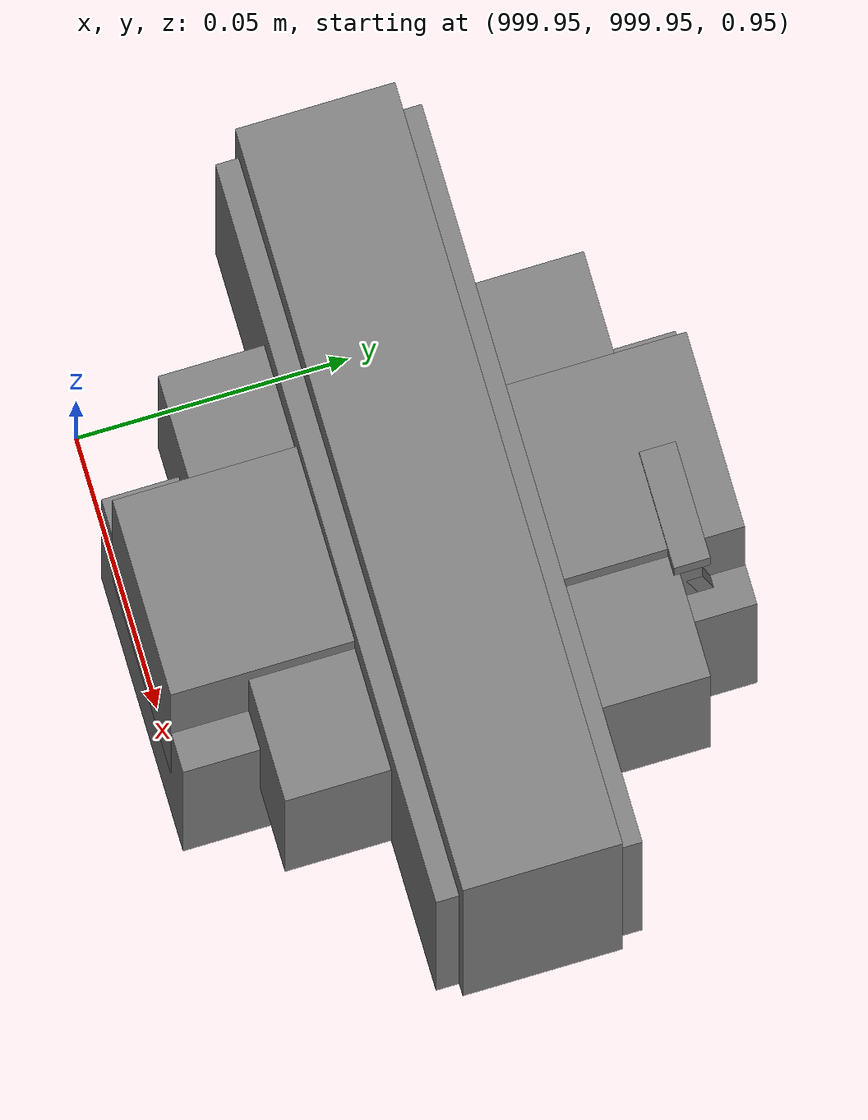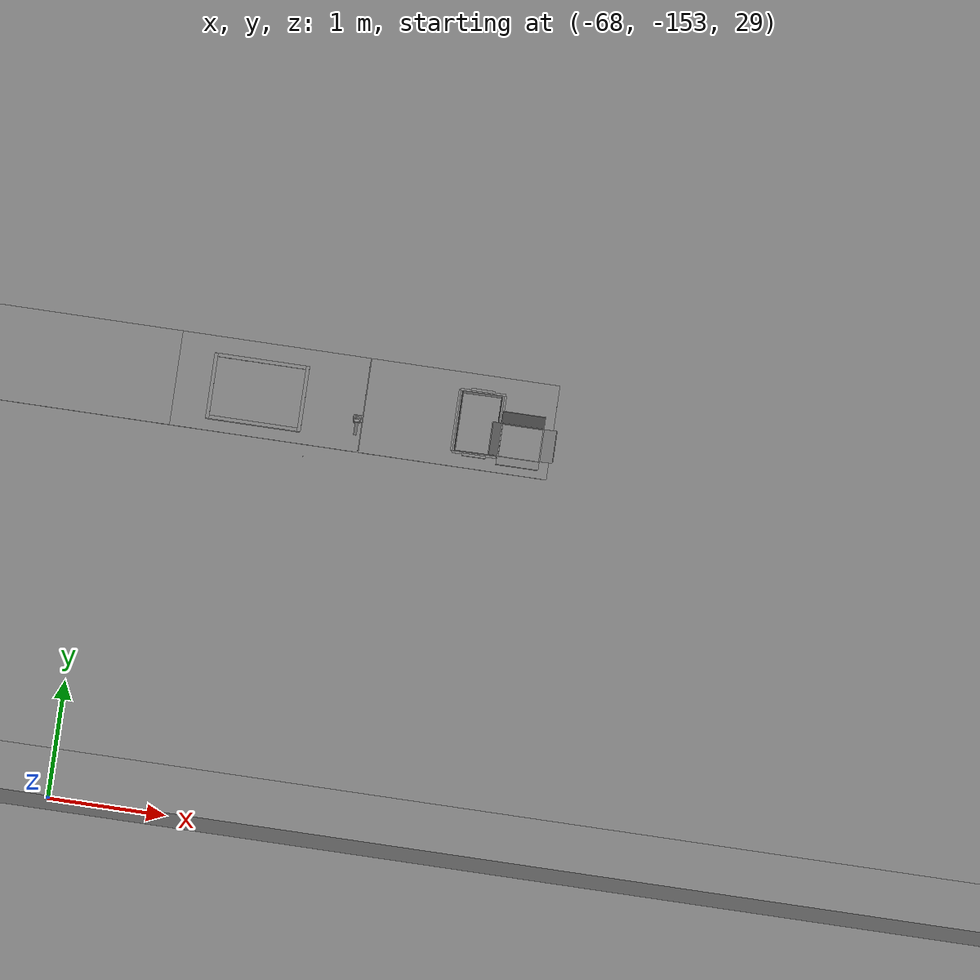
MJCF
<mujoco>
    <option gravity="0.000000000 0.000000000 -9.810000420" timestep="0.0049999999" integrator="implicitfast" density="1.225" viscosity="1.8000001e-05" noslip_iterations="10" iterations="100" sdf_iterations="50">
        <flag multiccd="disable"/>
    </option>
    <size memory="1000M"/>
    <compiler coordinate="local"/>
    <worldbody>
        <light cutoff="30" pos="0 1 1" dir="0 -1 -2"/>
        <light cutoff="30" pos="0 -1 1" dir="0 1 -2"/>
        <body pos="-64.866622925 -149.383972168 30.183746338" euler="89.999984741 89.999946594 0.000000000" name="openloong_gripper_2f85_fix_base_usda_bluebox_01">
            <geom contype="1" conaffinity="1" density="1000" type="box" material="" rgba="0.500000000 0.500000000 0.500000000 1.000000000" solimp="0.899999976 0.949999988 0.001000000" friction="1.000000000 0.005000000 0.000100000" solref="0.020000000 1.000000000" margin="0" condim="3" group="0" pos="0.276580811 0.187225342 0.000068665" quat="0.707106948 0.000077471 0.707106352 0.000077486" size="0.100000001 0.057999998 0.010000000" name="openloong_gripper_2f85_fix_base_usda_geom_19475291_A1BD_479C_9D6F_552C24FBA0CB"/>
            <geom contype="1" conaffinity="1" density="1000" type="box" material="" rgba="0.500000000 0.500000000 0.500000000 1.000000000" solimp="0.899999976 0.949999988 0.001000000" friction="1.000000000 0.005000000 0.000100000" solref="0.020000000 1.000000000" margin="0" condim="3" group="0" pos="0.000000000 0.002883911 0.000000000" quat="0.999999881 0.000000000 0.000000000 0.000000000" size="0.254000008 0.003000000 0.172000006" name="openloong_gripper_2f85_fix_base_usda_geom_A338D99E_175D_459C_9881_90A24432DD7A"/>
            <geom contype="1" conaffinity="1" density="1000" type="box" material="" rgba="0.500000000 0.500000000 0.500000000 1.000000000" solimp="0.899999976 0.949999988 0.001000000" friction="1.000000000 0.005000000 0.000100000" solref="0.020000000 1.000000000" margin="0" condim="3" group="0" pos="0.000000000 0.124874115 0.173484802" quat="0.999796331 0.020176515 -0.000000015 0.000000030" size="0.259999990 0.119999997 0.007000000" name="openloong_gripper_2f85_fix_base_usda_geom_3BFF5525_0143_4A1A_A403_FB55F751F9A1"/>
            <geom contype="1" conaffinity="1" density="1000" type="box" material="" rgba="0.500000000 0.500000000 0.500000000 1.000000000" solimp="0.899999976 0.949999988 0.001000000" friction="1.000000000 0.005000000 0.000100000" solref="0.020000000 1.000000000" margin="0" condim="3" group="0" pos="0.000000000 0.124874115 -0.173469543" quat="0.999796331 -0.020176545 -0.000000015 0.000000000" size="0.259999990 0.119999997 0.007000000" name="openloong_gripper_2f85_fix_base_usda_geom_597229EE_8CE3_4B69_88E3_29335624AC90"/>
            <geom contype="1" conaffinity="1" density="1000" type="box" material="" rgba="0.500000000 0.500000000 0.500000000 1.000000000" solimp="0.899999976 0.949999988 0.001000000" friction="1.000000000 0.005000000 0.000100000" solref="0.020000000 1.000000000" margin="0" condim="3" group="0" pos="0.000000000 0.214008331 0.188980103" quat="0.999912977 0.013176724 0.000000015 0.000000000" size="0.259999990 0.029999999 0.012500000" name="openloong_gripper_2f85_fix_base_usda_geom_BDE03DA2_53C9_4F86_B21C_A01E933D9ACF"/>
            <geom contype="1" conaffinity="1" density="1000" type="box" material="" rgba="0.500000000 0.500000000 0.500000000 1.000000000" solimp="0.899999976 0.949999988 0.001000000" friction="1.000000000 0.005000000 0.000100000" solref="0.020000000 1.000000000" margin="0" condim="3" group="0" pos="-0.258361816 0.125289917 0.001876831" quat="0.702796936 -0.020792112 0.710783124 0.020769298" size="0.189999998 0.119999997 0.009000000" name="openloong_gripper_2f85_fix_base_usda_geom_19D45CD9_2111_4E3D_BE98_4E6B13240F5B"/>
            <geom contype="1" conaffinity="1" density="1000" type="box" material="" rgba="0.500000000 0.500000000 0.500000000 1.000000000" solimp="0.899999976 0.949999988 0.001000000" friction="1.000000000 0.005000000 0.000100000" solref="0.020000000 1.000000000" margin="0" condim="3" group="0" pos="0.000000000 0.214008331 -0.188980103" quat="0.999912977 -0.013176769 0.000000030 0.000000015" size="0.259999990 0.029999999 0.012500000" name="openloong_gripper_2f85_fix_base_usda_geom_C410ED11_ED15_4349_8D21_115C56031D36"/>
            <geom contype="1" conaffinity="1" density="1000" type="box" material="" rgba="0.500000000 0.500000000 0.500000000 1.000000000" solimp="0.899999976 0.949999988 0.001000000" friction="1.000000000 0.005000000 0.000100000" solref="0.020000000 1.000000000" margin="0" condim="3" group="0" pos="-0.276611328 0.187225342 0.000068665" quat="0.707106650 0.000077441 0.707106709 0.000077456" size="0.100000001 0.057999998 0.010000000" name="openloong_gripper_2f85_fix_base_usda_geom_14DF24FE_599B_4356_A92A_1D0177B7E712"/>
            <geom contype="1" conaffinity="1" density="1000" type="box" material="" rgba="0.500000000 0.500000000 0.500000000 1.000000000" solimp="0.899999976 0.949999988 0.001000000" friction="1.000000000 0.005000000 0.000100000" solref="0.020000000 1.000000000" margin="0" condim="3" group="0" pos="0.258331299 0.125289917 0.001876831" quat="0.702851415 0.018856421 0.710823774 -0.019329369" size="0.189999998 0.119999997 0.009000000" name="openloong_gripper_2f85_fix_base_usda_geom_075D392A_E779_405B_AC1A_A87F8C0D8707"/>
            <freejoint name="openloong_gripper_2f85_fix_base_usda_bluebox_01_joint"/>
            <site size="0.005000000 0.005000000 0.005000000" rgba="0.500000000 0.500000000 0.500000000 1.000000000" pos="0.000000000 0.000000000 0.000000000" quat="0.999961913 0.008726534 0.000000000 0.000000000" group="0" type="sphere" name="openloong_gripper_2f85_fix_base_usda_bluebox_01site"/>
        </body>
        <body pos="-64.496299744 -149.491867065 30.235729218" euler="0.000000000 0.000000000 89.999946594" name="openloong_gripper_2f85_fix_base_usda_cardboardbox_01">
            <geom contype="1" conaffinity="1" density="1000" type="box" material="" rgba="0.500000000 0.500000000 0.500000000 1.000000000" solimp="0.899999976 0.949999988 0.001000000" friction="1.000000000 0.005000000 0.000100000" solref="0.020000000 1.000000000" margin="0" condim="3" group="0" pos="-0.003166199 -0.004086494 0.005052090" quat="1.000000000 0.000000000 0.000000000 0.000000000" size="0.142499998 0.177500010 0.005000000" name="openloong_gripper_2f85_fix_base_usda_geom_7D33238B_4306_4D56_AF78_E7117B02D556"/>
            <geom contype="1" conaffinity="1" density="1000" type="box" material="" rgba="0.500000000 0.500000000 0.500000000 1.000000000" solimp="0.899999976 0.949999988 0.001000000" friction="1.000000000 0.005000000 0.000100000" solref="0.020000000 1.000000000" margin="0" condim="3" group="0" pos="-0.003166199 0.170316696 0.150570869" quat="1.000000000 0.000000000 0.000000000 0.000000000" size="0.142499998 0.005000000 0.149999991" name="openloong_gripper_2f85_fix_base_usda_geom_4420679B_F015_471D_B208_6CB1693FE526"/>
            <geom contype="1" conaffinity="1" density="1000" type="box" material="" rgba="0.500000000 0.500000000 0.500000000 1.000000000" solimp="0.899999976 0.949999988 0.001000000" friction="1.000000000 0.005000000 0.000100000" solref="0.020000000 1.000000000" margin="0" condim="3" group="0" pos="-0.147399902 -0.005307198 0.150570869" quat="1.000000000 0.000000000 0.000000000 0.000000000" size="0.005000000 0.177500010 0.149999991" name="openloong_gripper_2f85_fix_base_usda_geom_6110099E_8AF3_4705_AA83_33947645CD86"/>
            <geom contype="1" conaffinity="1" density="1000" type="box" material="" rgba="0.500000000 0.500000000 0.500000000 1.000000000" solimp="0.899999976 0.949999988 0.001000000" friction="1.000000000 0.005000000 0.000100000" solref="0.020000000 1.000000000" margin="0" condim="3" group="0" pos="0.140275955 -0.005307198 0.150570869" quat="1.000000000 0.000000000 0.000000000 0.000000000" size="0.005000000 0.177500010 0.149999991" name="openloong_gripper_2f85_fix_base_usda_geom_69A0B521_D159_44BE_ACC9_6B2C5BED1644"/>
            <geom contype="1" conaffinity="1" density="1000" type="box" material="" rgba="0.500000000 0.500000000 0.500000000 1.000000000" solimp="0.899999976 0.949999988 0.001000000" friction="1.000000000 0.005000000 0.000100000" solref="0.020000000 1.000000000" margin="0" condim="3" group="0" pos="-0.003166199 -0.181550980 0.150570869" quat="1.000000000 0.000000000 0.000000000 0.000000000" size="0.142499998 0.005000000 0.149999991" name="openloong_gripper_2f85_fix_base_usda_geom_1CF6860A_A6F3_42AB_82F4_40A232B4E8C2"/>
            <freejoint name="openloong_gripper_2f85_fix_base_usda_cardboardbox_01_joint"/>
            <site size="0.005000000 0.005000000 0.005000000" rgba="0.500000000 0.500000000 0.500000000 1.000000000" pos="0.000000000 0.000000000 0.000000000" quat="0.999961913 0.008726535 0.000000000 0.000000000" group="0" type="sphere" name="openloong_gripper_2f85_fix_base_usda_site_007D2C37_6F2A_4B15_A341_96CFE6E71870"/>
            <body pos="0.139160156 -0.004048347 0.301930904" euler="-179.999954224 49.383502960 179.999954224" name="openloong_gripper_2f85_fix_base_usda_A1_006">
                <geom contype="1" conaffinity="1" density="1000" type="box" material="" rgba="0.500000000 0.500000000 0.500000000 1.000000000" solimp="0.899999976 0.949999988 0.001000000" friction="1.000000000 0.005000000 0.000100000" solref="0.020000000 1.000000000" margin="0" condim="3" group="0" pos="-0.071587563 0.000009537 0.001745224" quat="0.999999881 0.000000000 0.000000000 0.000000000" size="0.071249999 0.179999992 0.002500000" name="openloong_gripper_2f85_fix_base_usda_geom_AC6F4478_3C74_485C_9C65_22650BAEAB61"/>
                <joint armature="0" stiffness="0.07" damping="0.0099999998" axis="0.000000 1.000000 0.000000" type="hinge" name="openloong_gripper_2f85_fix_base_usda_A1_006"/>
            </body>
            <body pos="-0.145902634 -0.004086494 0.301938057" euler="-180.000000000 -60.000011444 -180.000000000" name="openloong_gripper_2f85_fix_base_usda_A2_006">
                <geom contype="1" conaffinity="1" density="1000" type="box" material="" rgba="0.500000000 0.500000000 0.500000000 1.000000000" solimp="0.899999976 0.949999988 0.001000000" friction="1.000000000 0.005000000 0.000100000" solref="0.020000000 1.000000000" margin="0" condim="3" group="0" pos="0.071268082 0.000009537 0.002717972" quat="0.000002921 0.000000000 -0.000000030 0.999999881" size="0.071249999 0.179999992 0.002500000" name="openloong_gripper_2f85_fix_base_usda_geom_3DA26F84_9BDE_4B1A_AD07_FAACDA7919EA"/>
                <joint armature="0" stiffness="0.07" damping="0.0099999998" axis="0.000000 1.000000 0.000000" type="hinge" name="openloong_gripper_2f85_fix_base_usda_A2_006"/>
            </body>
            <body pos="-0.003385544 0.175991058 0.301930904" euler="-125.858116150 -0.000004561 0.000002331" name="openloong_gripper_2f85_fix_base_usda_B2_006">
                <geom contype="1" conaffinity="1" density="1000" type="box" material="" rgba="0.500000000 0.500000000 0.500000000 1.000000000" solimp="0.899999976 0.949999988 0.001000000" friction="1.000000000 0.005000000 0.000100000" solref="0.020000000 1.000000000" margin="0" condim="3" group="0" pos="0.000009537 -0.070939064 -0.002470016" quat="0.999614120 0.027776197 -0.000000015 0.000000030" size="0.137500003 0.064999998 0.005000000" name="openloong_gripper_2f85_fix_base_usda_geom_B50E0FDD_48B2_400E_B556_1579E2D0A895"/>
                <joint armature="0" stiffness="0.07" damping="0.0099999998" axis="1.000000 0.000000 0.000000" type="hinge" name="openloong_gripper_2f85_fix_base_usda_B2_006"/>
            </body>
            <body pos="-0.003385544 -0.184140205 0.301938057" euler="147.805557251 0.000000000 0.000000000" name="openloong_gripper_2f85_fix_base_usda_B1_006">
                <geom contype="1" conaffinity="1" density="1000" type="box" material="" rgba="0.500000000 0.500000000 0.500000000 1.000000000" solimp="0.899999976 0.949999988 0.001000000" friction="1.000000000 0.005000000 0.000100000" solref="0.020000000 1.000000000" margin="0" condim="3" group="0" pos="-0.000028610 0.070202351 -0.002703667" quat="0.999614179 -0.027776167 0.000000000 0.000000000" size="0.137500003 0.064999998 0.005000000" name="openloong_gripper_2f85_fix_base_usda_geom_AFDCAA7B_3D25_496B_9A5C_D83573150A43"/>
                <joint armature="0" stiffness="0.07" damping="0.0099999998" axis="1.000000 0.000000 0.000000" type="hinge" name="openloong_gripper_2f85_fix_base_usda_B1_006"/>
            </body>
        </body>
        <body pos="-65.882858276 -149.481979370 30.229999542" euler="-64.487716675 0.000000000 0.000000000" name="openloong_gripper_2f85_fix_base_usda_Barcode">
            <geom contype="1" conaffinity="1" density="1000" type="box" material="" rgba="0.500000000 0.500000000 0.500000000 1.000000000" solimp="0.899999976 0.949999988 0.001000000" friction="1.000000000 0.005000000 0.000100000" solref="0.020000000 1.000000000" margin="0" condim="3" group="0" pos="0.000000000 0.013038635 0.001419067" quat="0.000000000 0.000000000 0.000000000 1.000000119" size="0.034000002 0.010000000 0.017999999" name="openloong_gripper_2f85_fix_base_usda_geom_BB2BDCF6_DBE7_4829_A43E_8170D8C3A03B"/>
            <geom contype="1" conaffinity="1" density="1000" type="box" material="" rgba="0.500000000 0.500000000 0.500000000 1.000000000" solimp="0.899999976 0.949999988 0.001000000" friction="1.000000000 0.005000000 0.000100000" solref="0.020000000 1.000000000" margin="0" condim="3" group="0" pos="0.000000000 -0.035301208 -0.007095337" quat="0.000000000 0.000000000 -0.043619365 0.999048233" size="0.028999999 0.010000000 0.020000000" name="openloong_gripper_2f85_fix_base_usda_geom_0289C8F4_8F96_437D_9199_5111FE33B715"/>
            <geom contype="1" conaffinity="1" density="1000" type="box" material="" rgba="0.500000000 0.500000000 0.500000000 1.000000000" solimp="0.899999976 0.949999988 0.001000000" friction="1.000000000 0.005000000 0.000100000" solref="0.020000000 1.000000000" margin="0" condim="3" group="0" pos="0.000000000 -0.043411255 -0.011749268" quat="0.922262907 0.386563420 0.000000000 0.000000000" size="0.026000001 0.010000000 0.020000000" name="openloong_gripper_2f85_fix_base_usda_geom_2CAD67F7_16F6_4CC3_B903_8071265D01B5"/>
            <geom contype="1" conaffinity="1" density="1000" type="box" material="" rgba="0.500000000 0.500000000 0.500000000 1.000000000" solimp="0.899999976 0.949999988 0.001000000" friction="1.000000000 0.005000000 0.000100000" solref="0.020000000 1.000000000" margin="0" condim="3" group="0" pos="0.000000000 -0.016967773 -0.031860352" quat="0.000000000 0.000000000 0.000000000 1.000000119" size="0.008000000 0.010000000 0.013000000" name="openloong_gripper_2f85_fix_base_usda_geom_D24923F5_6D1B_4766_85AB_C1BFD1E07210"/>
            <geom contype="1" conaffinity="1" density="1000" type="box" material="" rgba="0.500000000 0.500000000 0.500000000 1.000000000" solimp="0.899999976 0.949999988 0.001000000" friction="1.000000000 0.005000000 0.000100000" solref="0.020000000 1.000000000" margin="0" condim="3" group="0" pos="0.000000000 -0.001869202 0.000312805" quat="0.953716993 0.300705761 0.000000000 0.000000000" size="0.032000002 0.010000000 0.018999999" name="openloong_gripper_2f85_fix_base_usda_geom_5E25BD86_AEB2_42B5_91D1_0A68EABD0274"/>
            <geom contype="1" conaffinity="1" density="1000" type="box" material="" rgba="0.500000000 0.500000000 0.500000000 1.000000000" solimp="0.899999976 0.949999988 0.001000000" friction="1.000000000 0.005000000 0.000100000" solref="0.020000000 1.000000000" margin="0" condim="3" group="0" pos="0.000000000 -0.019531250 -0.003173828" quat="0.953716993 0.300705761 0.000000000 0.000000000" size="0.030999999 0.010000000 0.020000000" name="openloong_gripper_2f85_fix_base_usda_geom_50B908B1_32E2_4A61_B52C_BBEA87C522A5"/>
            <geom contype="1" conaffinity="1" density="1000" type="box" material="" rgba="0.500000000 0.500000000 0.500000000 1.000000000" solimp="0.899999976 0.949999988 0.001000000" friction="1.000000000 0.005000000 0.000100000" solref="0.020000000 1.000000000" margin="0" condim="3" group="0" pos="0.000000000 -0.035301208 -0.007095337" quat="0.953716993 0.300705761 0.000000000 0.000000000" size="0.028999999 0.010000000 0.020000000" name="openloong_gripper_2f85_fix_base_usda_geom_0AAECD3A_C948_4840_963E_1C58596C03C3"/>
            <geom contype="1" conaffinity="1" density="1000" type="box" material="" rgba="0.500000000 0.500000000 0.500000000 1.000000000" solimp="0.899999976 0.949999988 0.001000000" friction="1.000000000 0.005000000 0.000100000" solref="0.020000000 1.000000000" margin="0" condim="3" group="0" pos="0.000000000 -0.042617798 -0.071121216" quat="0.000000000 0.000000000 0.000000000 1.000000119" size="0.013000000 0.021000000 0.059999999" name="openloong_gripper_2f85_fix_base_usda_geom_62E08EFE_15A0_4938_8028_A80DE6B876C5"/>
            <freejoint name="openloong_gripper_2f85_fix_base_usda_Barcode_joint"/>
            <site size="0.005000000 0.005000000 0.005000000" rgba="0.500000000 0.500000000 0.500000000 1.000000000" pos="0.000000000 0.000000000 0.000000000" quat="1.000000000 0.000000000 0.000000000 0.000000000" group="0" type="sphere" name="openloong_gripper_2f85_fix_base_usda_Barcode_site"/>
        </body>
        <body pos="-66.745018005 -149.392349243 30.184000015" euler="0.000000000 0.000000000 89.999946594" name="[22330797463536]_Basket_01">
            <geom contype="1" conaffinity="1" density="1000" type="box" material="" rgba="0.500000000 0.500000000 0.500000000 1.000000000" solimp="0.899999976 0.949999988 0.001000000" friction="1.000000000 0.005000000 0.000100000" solref="0.020000000 1.000000000" margin="0" condim="3" group="0" pos="-0.052425385 0.389207840 0.089787483" quat="0.707107008 0.000000000 0.000000000 0.707106411" size="0.014249999 0.014249999 0.059999999" name="[22330797463536]_geom_620115B6_1B9C_4CE9_8027_678A5A4710E2"/>
            <geom contype="1" conaffinity="1" density="1000" type="box" material="" rgba="0.500000000 0.500000000 0.500000000 1.000000000" solimp="0.899999976 0.949999988 0.001000000" friction="1.000000000 0.005000000 0.000100000" solref="0.020000000 1.000000000" margin="0" condim="3" group="0" pos="0.264015198 -0.133043289 0.089787483" quat="0.707107008 0.000000000 0.000000000 0.707106411" size="0.014249999 0.014249999 0.059999999" name="[22330797463536]_geom_D5F872C7_2612_4627_A987_C3E232648AB0"/>
            <geom contype="1" conaffinity="1" density="1000" type="box" material="" rgba="0.500000000 0.500000000 0.500000000 1.000000000" solimp="0.899999976 0.949999988 0.001000000" friction="1.000000000 0.005000000 0.000100000" solref="0.020000000 1.000000000" margin="0" condim="3" group="0" pos="-0.264015198 -0.265548706 0.089793205" quat="0.707107008 0.000000000 0.000000000 0.707106411" size="0.014249999 0.014249999 0.059999999" name="[22330797463536]_geom_AEF1BB01_AF07_4246_A1B0_6B77D07AFDDD"/>
            <geom contype="1" conaffinity="1" density="1000" type="box" material="" rgba="0.500000000 0.500000000 0.500000000 1.000000000" solimp="0.899999976 0.949999988 0.001000000" friction="1.000000000 0.005000000 0.000100000" solref="0.020000000 1.000000000" margin="0" condim="3" group="0" pos="-0.160263062 -0.389322281 0.089793205" quat="0.707107008 0.000000000 0.000000000 0.707106411" size="0.014249999 0.014249999 0.059999999" name="[22330797463536]_geom_9A36CA51_91CD_4EBE_9264_384B9AC432B3"/>
            <geom contype="1" conaffinity="1" density="1000" type="box" material="" rgba="0.500000000 0.500000000 0.500000000 1.000000000" solimp="0.899999976 0.949999988 0.001000000" friction="1.000000000 0.005000000 0.000100000" solref="0.020000000 1.000000000" margin="0" condim="3" group="0" pos="0.162265778 -0.389322281 0.089787483" quat="0.707107008 0.000000000 0.000000000 0.707106411" size="0.014249999 0.014249999 0.059999999" name="[22330797463536]_geom_1A2F2FA2_0558_4C1D_81CC_6CDB26FC77FF"/>
            <geom contype="1" conaffinity="1" density="1000" type="box" material="" rgba="0.500000000 0.500000000 0.500000000 1.000000000" solimp="0.899999976 0.949999988 0.001000000" friction="1.000000000 0.005000000 0.000100000" solref="0.020000000 1.000000000" margin="0" condim="3" group="0" pos="0.264015198 0.389207840 0.089787483" quat="0.707107008 0.000000000 0.000000000 0.707106411" size="0.014249999 0.014249999 0.059999999" name="[22330797463536]_geom_E315FE28_CBB3_47B7_94B5_D3A747AFAF45"/>
            <geom contype="1" conaffinity="1" density="1000" type="box" material="" rgba="0.500000000 0.500000000 0.500000000 1.000000000" solimp="0.899999976 0.949999988 0.001000000" friction="1.000000000 0.005000000 0.000100000" solref="0.020000000 1.000000000" margin="0" condim="3" group="0" pos="-0.264015198 -0.133043289 0.089793205" quat="0.707107008 0.000000000 0.000000000 0.707106411" size="0.014249999 0.014249999 0.059999999" name="[22330797463536]_geom_57AF91B1_E63D_4E6F_8007_DDD5B303B2B4"/>
            <geom contype="1" conaffinity="1" density="1000" type="box" material="" rgba="0.500000000 0.500000000 0.500000000 1.000000000" solimp="0.899999976 0.949999988 0.001000000" friction="1.000000000 0.005000000 0.000100000" solref="0.020000000 1.000000000" margin="0" condim="3" group="0" pos="-0.264026642 0.269256592 0.089793205" quat="0.707107008 0.000000000 0.000000000 0.707106411" size="0.014249999 0.014249999 0.059999999" name="[22330797463536]_geom_0725F7FE_5FCC_4C60_87FC_40452D381798"/>
            <geom contype="1" conaffinity="1" density="1000" type="box" material="" rgba="0.500000000 0.500000000 0.500000000 1.000000000" solimp="0.899999976 0.949999988 0.001000000" friction="1.000000000 0.005000000 0.000100000" solref="0.020000000 1.000000000" margin="0" condim="3" group="0" pos="0.054462433 0.389207840 0.089787483" quat="0.707107008 0.000000000 0.000000000 0.707106411" size="0.014249999 0.014249999 0.059999999" name="[22330797463536]_geom_497010FD_E79F_4FAC_9C33_3F03F803C231"/>
            <geom contype="1" conaffinity="1" density="1000" type="box" material="" rgba="0.500000000 0.500000000 0.500000000 1.000000000" solimp="0.899999976 0.949999988 0.001000000" friction="1.000000000 0.005000000 0.000100000" solref="0.020000000 1.000000000" margin="0" condim="3" group="0" pos="0.054462433 -0.389322281 0.089787483" quat="0.707107008 0.000000000 0.000000000 0.707106411" size="0.014249999 0.014249999 0.059999999" name="[22330797463536]_geom_569B6084_8AE9_4FC7_A7A7_FF4230981A7F"/>
            <geom contype="1" conaffinity="1" density="1000" type="box" material="" rgba="0.500000000 0.500000000 0.500000000 1.000000000" solimp="0.899999976 0.949999988 0.001000000" friction="1.000000000 0.005000000 0.000100000" solref="0.020000000 1.000000000" margin="0" condim="3" group="0" pos="0.264015198 0.269256592 0.089793205" quat="0.707107008 0.000000000 0.000000000 0.707106411" size="0.014249999 0.014249999 0.059999999" name="[22330797463536]_geom_ED47C0E9_3396_40EA_B1F5_0EABDD2661BE"/>
            <geom contype="1" conaffinity="1" density="1000" type="box" material="" rgba="0.500000000 0.500000000 0.500000000 1.000000000" solimp="0.899999976 0.949999988 0.001000000" friction="1.000000000 0.005000000 0.000100000" solref="0.020000000 1.000000000" margin="0" condim="3" group="0" pos="0.264015198 -0.389322281 0.089787483" quat="0.707107008 0.000000000 0.000000000 0.707106411" size="0.014249999 0.014249999 0.059999999" name="[22330797463536]_geom_624CF6BF_8FBB_4381_8507_E8A90BDC49FF"/>
            <geom contype="1" conaffinity="1" density="1000" type="box" material="" rgba="0.500000000 0.500000000 0.500000000 1.000000000" solimp="0.899999976 0.949999988 0.001000000" friction="1.000000000 0.005000000 0.000100000" solref="0.020000000 1.000000000" margin="0" condim="3" group="0" pos="0.000000000 0.000000000 0.015998840" quat="0.707107008 0.000000000 0.000000000 0.707106411" size="0.403499991 0.279000014 0.015750000" name="[22330797463536]_geom_1A6335B8_FFBF_47D2_B467_F2D4185FC222"/>
            <geom contype="1" conaffinity="1" density="1000" type="box" material="" rgba="0.500000000 0.500000000 0.500000000 1.000000000" solimp="0.899999976 0.949999988 0.001000000" friction="1.000000000 0.005000000 0.000100000" solref="0.020000000 1.000000000" margin="0" condim="3" group="0" pos="0.000000000 -0.389476776 0.163619041" quat="0.707107008 0.000000000 0.000000000 0.707106411" size="0.015000000 0.277500004 0.015750000" name="[22330797463536]_geom_62E42E3E_FDE7_46C3_A272_1D6286A2D40D"/>
            <geom contype="1" conaffinity="1" density="1000" type="box" material="" rgba="0.500000000 0.500000000 0.500000000 1.000000000" solimp="0.899999976 0.949999988 0.001000000" friction="1.000000000 0.005000000 0.000100000" solref="0.020000000 1.000000000" margin="0" condim="3" group="0" pos="0.162265778 0.389207840 0.089787483" quat="0.707107008 0.000000000 0.000000000 0.707106411" size="0.014249999 0.014249999 0.059999999" name="[22330797463536]_geom_DB2D8EB4_815F_408C_B633_8713C58EA4AB"/>
            <geom contype="1" conaffinity="1" density="1000" type="box" material="" rgba="0.500000000 0.500000000 0.500000000 1.000000000" solimp="0.899999976 0.949999988 0.001000000" friction="1.000000000 0.005000000 0.000100000" solref="0.020000000 1.000000000" margin="0" condim="3" group="0" pos="0.000000000 0.389471054 0.163619041" quat="0.707107008 0.000000000 0.000000000 0.707106411" size="0.015000000 0.277500004 0.015750000" name="[22330797463536]_geom_73E34FEC_6DFB_49A8_93DD_117E35CEF336"/>
            <geom contype="1" conaffinity="1" density="1000" type="box" material="" rgba="0.500000000 0.500000000 0.500000000 1.000000000" solimp="0.899999976 0.949999988 0.001000000" friction="1.000000000 0.005000000 0.000100000" solref="0.020000000 1.000000000" margin="0" condim="3" group="0" pos="-0.263511658 0.000000000 0.163619041" quat="0.707107008 0.000000000 0.000000000 0.707106411" size="0.403499991 0.015000000 0.015750000" name="[22330797463536]_geom_55A1367B_5A33_4CD4_BF77_31BB3C9A795C"/>
            <geom contype="1" conaffinity="1" density="1000" type="box" material="" rgba="0.500000000 0.500000000 0.500000000 1.000000000" solimp="0.899999976 0.949999988 0.001000000" friction="1.000000000 0.005000000 0.000100000" solref="0.020000000 1.000000000" margin="0" condim="3" group="0" pos="-0.264015198 0.141334534 0.089793205" quat="0.707107008 0.000000000 0.000000000 0.707106411" size="0.014249999 0.014249999 0.059999999" name="[22330797463536]_geom_8BEB6A76_9D30_421A_8AC9_FBF752921416"/>
            <geom contype="1" conaffinity="1" density="1000" type="box" material="" rgba="0.500000000 0.500000000 0.500000000 1.000000000" solimp="0.899999976 0.949999988 0.001000000" friction="1.000000000 0.005000000 0.000100000" solref="0.020000000 1.000000000" margin="0" condim="3" group="0" pos="0.264015198 -0.265548706 0.089787483" quat="0.707107008 0.000000000 0.000000000 0.707106411" size="0.014249999 0.014249999 0.059999999" name="[22330797463536]_geom_D78509CB_71C4_42DB_9107_9956770FD5DA"/>
            <geom contype="1" conaffinity="1" density="1000" type="box" material="" rgba="0.500000000 0.500000000 0.500000000 1.000000000" solimp="0.899999976 0.949999988 0.001000000" friction="1.000000000 0.005000000 0.000100000" solref="0.020000000 1.000000000" margin="0" condim="3" group="0" pos="-0.160263062 0.389207840 0.089787483" quat="0.707107008 0.000000000 0.000000000 0.707106411" size="0.014249999 0.014249999 0.059999999" name="[22330797463536]_geom_F06254CB_FC0C_4B8F_A22A_4F363181E99A"/>
            <geom contype="1" conaffinity="1" density="1000" type="box" material="" rgba="0.500000000 0.500000000 0.500000000 1.000000000" solimp="0.899999976 0.949999988 0.001000000" friction="1.000000000 0.005000000 0.000100000" solref="0.020000000 1.000000000" margin="0" condim="3" group="0" pos="-0.052425385 -0.389322281 0.089787483" quat="0.707107008 0.000000000 0.000000000 0.707106411" size="0.014249999 0.014249999 0.059999999" name="[22330797463536]_geom_0534374E_926F_43D3_8BF2_D086FD2D083D"/>
            <geom contype="1" conaffinity="1" density="1000" type="box" material="" rgba="0.500000000 0.500000000 0.500000000 1.000000000" solimp="0.899999976 0.949999988 0.001000000" friction="1.000000000 0.005000000 0.000100000" solref="0.020000000 1.000000000" margin="0" condim="3" group="0" pos="-0.264026642 -0.389322281 0.089793205" quat="0.707107008 0.000000000 0.000000000 0.707106411" size="0.014249999 0.014249999 0.059999999" name="[22330797463536]_geom_73DF6F89_B3AB_49A2_99D5_2320A5857F74"/>
            <geom contype="1" conaffinity="1" density="1000" type="box" material="" rgba="0.500000000 0.500000000 0.500000000 1.000000000" solimp="0.899999976 0.949999988 0.001000000" friction="1.000000000 0.005000000 0.000100000" solref="0.020000000 1.000000000" margin="0" condim="3" group="0" pos="0.264015198 0.141334534 0.089787483" quat="0.707107008 0.000000000 0.000000000 0.707106411" size="0.014249999 0.014249999 0.059999999" name="[22330797463536]_geom_AC391818_4B6B_48E1_AE2C_4FFE2443B121"/>
            <geom contype="1" conaffinity="1" density="1000" type="box" material="" rgba="0.500000000 0.500000000 0.500000000 1.000000000" solimp="0.899999976 0.949999988 0.001000000" friction="1.000000000 0.005000000 0.000100000" solref="0.020000000 1.000000000" margin="0" condim="3" group="0" pos="-0.264015198 0.389207840 0.089793205" quat="0.707107008 0.000000000 0.000000000 0.707106411" size="0.014249999 0.014249999 0.059999999" name="[22330797463536]_geom_13481145_269E_4B0D_A37C_6A7E246092E2"/>
            <geom contype="1" conaffinity="1" density="1000" type="box" material="" rgba="0.500000000 0.500000000 0.500000000 1.000000000" solimp="0.899999976 0.949999988 0.001000000" friction="1.000000000 0.005000000 0.000100000" solref="0.020000000 1.000000000" margin="0" condim="3" group="0" pos="0.264015198 0.004480362 0.089787483" quat="0.707107008 0.000000000 0.000000000 0.707106411" size="0.014249999 0.014249999 0.059999999" name="[22330797463536]_geom_D127644B_A4D8_4786_A178_C63135AD0ABA"/>
            <geom contype="1" conaffinity="1" density="1000" type="box" material="" rgba="0.500000000 0.500000000 0.500000000 1.000000000" solimp="0.899999976 0.949999988 0.001000000" friction="1.000000000 0.005000000 0.000100000" solref="0.020000000 1.000000000" margin="0" condim="3" group="0" pos="0.263694763 -0.000011444 0.163619041" quat="0.707107008 0.000000000 0.000000000 0.707106411" size="0.403499991 0.015000000 0.015750000" name="[22330797463536]_geom_D6CFC2B1_2F99_40FE_AFF4_218745CA8B10"/>
            <geom contype="1" conaffinity="1" density="1000" type="box" material="" rgba="0.500000000 0.500000000 0.500000000 1.000000000" solimp="0.899999976 0.949999988 0.001000000" friction="1.000000000 0.005000000 0.000100000" solref="0.020000000 1.000000000" margin="0" condim="3" group="0" pos="-0.264015198 0.004480362 0.089793205" quat="0.707107008 0.000000000 0.000000000 0.707106411" size="0.014249999 0.014249999 0.059999999" name="[22330797463536]_geom_551623F8_A0FE_4D5C_8F80_88665B8A491D"/>
            <freejoint name="[22330797463536]_joint_0A25F970_3B91_4D30_8BCB_6D1D4C0D783B"/>
        </body>
        <body pos="0.000000000 0.000000000 0.000000000" euler="0.000000000 0.000000000 0.000000000" name="Static Objects_Static Objects">
            <geom contype="1" conaffinity="1" density="1000" type="box" material="" rgba="0.500000000 0.500000000 0.500000000 1.000000000" solimp="0.899999976 0.949999988 0.001000000" friction="1.000000000 0.005000000 0.000100000" solref="0.020000000 1.000000000" margin="0" condim="3" group="0" pos="-67.544113159 -149.365814209 29.727830887" quat="0.500000417 0.499999970 0.499999553 0.499999970" size="0.381000012 0.319999993 0.041000001" name="Static Objects_geom_EAF8B3BC_FE48_4FC1_924E_DC5D090D781B"/>
            <geom contype="1" conaffinity="1" density="1000" type="box" material="" rgba="0.500000000 0.500000000 0.500000000 1.000000000" solimp="0.899999976 0.949999988 0.001000000" friction="1.000000000 0.005000000 0.000100000" solref="0.020000000 1.000000000" margin="0" condim="3" group="0" pos="-68.239501953 -149.365814209 30.086868286" quat="0.500000417 0.499999970 0.499999553 0.499999970" size="0.370999992 0.039500002 0.745000005" name="Static Objects_geom_6D89667A_7F18_4CD3_AC55_A4ED56300CD2"/>
            <geom contype="1" conaffinity="1" density="1000" type="box" material="" rgba="0.500000000 0.500000000 0.500000000 1.000000000" solimp="0.899999976 0.949999988 0.001000000" friction="1.000000000 0.005000000 0.000100000" solref="0.020000000 1.000000000" margin="0" condim="3" group="0" pos="-68.239501953 -149.365814209 30.147235870" quat="0.500000417 0.499999970 0.499999553 0.499999970" size="0.400000006 0.022000000 0.800000012" name="Static Objects_geom_DC16CCD7_CB0C_416B_A685_3B2A53FCCE20"/>
            <geom contype="1" conaffinity="1" density="1000" type="box" material="" rgba="0.500000000 0.500000000 0.500000000 1.000000000" solimp="0.899999976 0.949999988 0.001000000" friction="1.000000000 0.005000000 0.000100000" solref="0.020000000 1.000000000" margin="0" condim="3" group="0" pos="-68.934890747 -149.365814209 29.727830887" quat="0.500000417 0.499999970 0.499999553 0.499999970" size="0.381000012 0.319999993 0.041000001" name="Static Objects_geom_754173E6_BAD8_471D_AAC1_814E53080F4E"/>
            <geom contype="1" conaffinity="1" density="1000" type="box" material="" rgba="0.500000000 0.500000000 0.500000000 1.000000000" solimp="0.899999976 0.949999988 0.001000000" friction="1.000000000 0.005000000 0.000100000" solref="0.020000000 1.000000000" margin="0" condim="3" group="0" pos="-68.239501953 -149.365814209 29.561563492" quat="0.500000417 0.499999970 0.499999553 0.499999970" size="0.020000000 0.022000000 0.660000026" name="Static Objects_geom_D2B1D536_654D_4EA7_BC93_2B89B621BC9C"/>
            <geom contype="1" conaffinity="1" density="1000" type="box" material="" rgba="0.500000000 0.500000000 0.500000000 1.000000000" solimp="0.899999976 0.949999988 0.001000000" friction="1.000000000 0.005000000 0.000100000" solref="0.020000000 1.000000000" margin="0" condim="3" group="0" pos="-65.945671082 -149.365814209 29.727830887" quat="0.500000417 0.499999970 0.499999553 0.499999970" size="0.381000012 0.319999993 0.041000001" name="Static Objects_geom_4C7DBDAA_5AD1_4BB8_B21D_4EADD331A463"/>
            <geom contype="1" conaffinity="1" density="1000" type="box" material="" rgba="0.500000000 0.500000000 0.500000000 1.000000000" solimp="0.899999976 0.949999988 0.001000000" friction="1.000000000 0.005000000 0.000100000" solref="0.020000000 1.000000000" margin="0" condim="3" group="0" pos="-66.641059875 -149.365814209 30.086868286" quat="0.500000417 0.499999970 0.499999553 0.499999970" size="0.370999992 0.039500002 0.745000005" name="Static Objects_geom_2D4BCD7E_D83B_4A13_9894_980EA130AE4F"/>
            <geom contype="1" conaffinity="1" density="1000" type="box" material="" rgba="0.500000000 0.500000000 0.500000000 1.000000000" solimp="0.899999976 0.949999988 0.001000000" friction="1.000000000 0.005000000 0.000100000" solref="0.020000000 1.000000000" margin="0" condim="3" group="0" pos="-66.641059875 -149.365814209 30.147235870" quat="0.500000417 0.499999970 0.499999553 0.499999970" size="0.400000006 0.022000000 0.800000012" name="Static Objects_geom_B6500D35_4546_4E7D_9D06_09345BC20115"/>
            <geom contype="1" conaffinity="1" density="1000" type="box" material="" rgba="0.500000000 0.500000000 0.500000000 1.000000000" solimp="0.899999976 0.949999988 0.001000000" friction="1.000000000 0.005000000 0.000100000" solref="0.020000000 1.000000000" margin="0" condim="3" group="0" pos="-67.336448669 -149.365814209 29.727830887" quat="0.500000417 0.499999970 0.499999553 0.499999970" size="0.381000012 0.319999993 0.041000001" name="Static Objects_geom_69BBFA8B_7870_416B_9370_C650C3611ADF"/>
            <geom contype="1" conaffinity="1" density="1000" type="box" material="" rgba="0.500000000 0.500000000 0.500000000 1.000000000" solimp="0.899999976 0.949999988 0.001000000" friction="1.000000000 0.005000000 0.000100000" solref="0.020000000 1.000000000" margin="0" condim="3" group="0" pos="-66.641059875 -149.365814209 29.561563492" quat="0.500000417 0.499999970 0.499999553 0.499999970" size="0.020000000 0.022000000 0.660000026" name="Static Objects_geom_DFDAC83A_6620_40FE_857D_32569A64B188"/>
            <geom contype="1" conaffinity="1" density="1000" type="box" material="" rgba="0.500000000 0.500000000 0.500000000 1.000000000" solimp="0.899999976 0.949999988 0.001000000" friction="1.000000000 0.005000000 0.000100000" solref="0.020000000 1.000000000" margin="0" condim="3" group="0" pos="-64.338577271 -149.365814209 29.727830887" quat="0.500000417 0.499999970 0.499999553 0.499999970" size="0.381000012 0.319999993 0.041000001" name="Static Objects_geom_6ABBBC33_703F_4EC0_90C2_B5B776CB3D52"/>
            <geom contype="1" conaffinity="1" density="1000" type="box" material="" rgba="0.500000000 0.500000000 0.500000000 1.000000000" solimp="0.899999976 0.949999988 0.001000000" friction="1.000000000 0.005000000 0.000100000" solref="0.020000000 1.000000000" margin="0" condim="3" group="0" pos="-65.033966064 -149.365814209 30.086868286" quat="0.500000417 0.499999970 0.499999553 0.499999970" size="0.370999992 0.039500002 0.745000005" name="Static Objects_geom_0BB328E2_B1CD_4C38_96D7_A6C4A28051C0"/>
            <geom contype="1" conaffinity="1" density="1000" type="box" material="" rgba="0.500000000 0.500000000 0.500000000 1.000000000" solimp="0.899999976 0.949999988 0.001000000" friction="1.000000000 0.005000000 0.000100000" solref="0.020000000 1.000000000" margin="0" condim="3" group="0" pos="-65.033966064 -149.365814209 30.147235870" quat="0.500000417 0.499999970 0.499999553 0.499999970" size="0.400000006 0.022000000 0.800000012" name="Static Objects_geom_F496B7F1_D602_4376_9A3A_97BFEBEC19C1"/>
            <geom contype="1" conaffinity="1" density="1000" type="box" material="" rgba="0.500000000 0.500000000 0.500000000 1.000000000" solimp="0.899999976 0.949999988 0.001000000" friction="1.000000000 0.005000000 0.000100000" solref="0.020000000 1.000000000" margin="0" condim="3" group="0" pos="-65.729354858 -149.365814209 29.727830887" quat="0.500000417 0.499999970 0.499999553 0.499999970" size="0.381000012 0.319999993 0.041000001" name="Static Objects_geom_1DFE935E_F68D_452C_A906_534CD6A31506"/>
            <geom contype="1" conaffinity="1" density="1000" type="box" material="" rgba="0.500000000 0.500000000 0.500000000 1.000000000" solimp="0.899999976 0.949999988 0.001000000" friction="1.000000000 0.005000000 0.000100000" solref="0.020000000 1.000000000" margin="0" condim="3" group="0" pos="-65.033966064 -149.365814209 29.561563492" quat="0.500000417 0.499999970 0.499999553 0.499999970" size="0.020000000 0.022000000 0.660000026" name="Static Objects_geom_9F355484_34CA_4B69_9613_C001DE8AA5FD"/>
            <geom contype="1" conaffinity="1" density="1000" type="box" material="" rgba="0.500000000 0.500000000 0.500000000 1.000000000" solimp="0.899999976 0.949999988 0.001000000" friction="1.000000000 0.005000000 0.000100000" solref="0.020000000 1.000000000" margin="0" condim="3" group="0" pos="-61.754566193 -137.853729248 33.906845093" quat="0.707107067 0.000000000 0.000000000 0.707106471" size="0.759999990 0.759999990 4.500000000" name="Static Objects_geom_BF52E6A8_22E9_4BCD_B370_7D011460602A"/>
            <geom contype="1" conaffinity="1" density="1000" type="box" material="" rgba="0.500000000 0.500000000 0.500000000 1.000000000" solimp="0.899999976 0.949999988 0.001000000" friction="1.000000000 0.005000000 0.000100000" solref="0.020000000 1.000000000" margin="0" condim="3" group="0" pos="-57.511135101 -144.927108765 31.707921982" quat="1.000000000 0.000000000 0.000000000 0.000000000" size="0.200000003 8.000000000 2.299999952" name="Static Objects_geom_B5F27158_C3A9_4D0B_9AC6_DA13D65EA822"/>
            <geom contype="1" conaffinity="1" density="1000" type="box" material="" rgba="0.500000000 0.500000000 0.500000000 1.000000000" solimp="0.899999976 0.949999988 0.001000000" friction="1.000000000 0.005000000 0.000100000" solref="0.020000000 1.000000000" margin="0" condim="3" group="0" pos="-80.517646790 -157.574050903 31.688196182" quat="0.707107067 0.000000000 0.000000000 0.707106471" size="0.600000024 0.600000024 2.299999952" name="Static Objects_geom_EE28B117_1F82_4955_8545_3CC8A2733204"/>
            <geom contype="1" conaffinity="1" density="1000" type="box" material="" rgba="0.500000000 0.500000000 0.500000000 1.000000000" solimp="0.899999976 0.949999988 0.001000000" friction="1.000000000 0.005000000 0.000100000" solref="0.020000000 1.000000000" margin="0" condim="3" group="0" pos="-80.711044312 -147.414932251 31.666158676" quat="1.000000000 0.000000000 0.000000000 0.000000000" size="0.200000003 10.000000000 2.299999952" name="Static Objects_geom_CB1FD28C_2CFD_49E2_903F_BE08409978B1"/>
            <geom contype="1" conaffinity="1" density="1000" type="box" material="" rgba="0.500000000 0.500000000 0.500000000 1.000000000" solimp="0.899999976 0.949999988 0.001000000" friction="1.000000000 0.005000000 0.000100000" solref="0.020000000 1.000000000" margin="0" condim="3" group="0" pos="-57.687217712 -137.434692383 31.688196182" quat="0.707107067 0.000000000 0.000000000 0.707106471" size="0.600000024 0.600000024 2.299999952" name="Static Objects_geom_71F04492_5122_4DEA_81D6_E728A2DA7C4E"/>
            <geom contype="1" conaffinity="1" density="1000" type="box" material="" rgba="0.500000000 0.500000000 0.500000000 1.000000000" solimp="0.899999976 0.949999988 0.001000000" friction="1.000000000 0.005000000 0.000100000" solref="0.020000000 1.000000000" margin="0" condim="3" group="0" pos="-69.537033081 -140.263229370 31.714921951" quat="0.707107067 0.000000000 0.000000000 0.707106471" size="0.759999990 4.500000000 2.299999952" name="Static Objects_geom_B196C507_4559_42C3_8DDC_283F64047F66"/>
            <geom contype="1" conaffinity="1" density="1000" type="box" material="" rgba="0.500000000 0.500000000 0.500000000 1.000000000" solimp="0.899999976 0.949999988 0.001000000" friction="1.000000000 0.005000000 0.000100000" solref="0.020000000 1.000000000" margin="0" condim="3" group="0" pos="-80.073638916 -137.853713989 33.906845093" quat="0.707107067 0.000000000 0.000000000 0.707106471" size="0.759999990 0.759999990 4.500000000" name="Static Objects_geom_9CCDED38_9669_4B8D_BAE8_F30CEA87BC6E"/>
            <geom contype="1" conaffinity="1" density="1000" type="box" material="" rgba="0.500000000 0.500000000 0.500000000 1.000000000" solimp="0.899999976 0.949999988 0.001000000" friction="1.000000000 0.005000000 0.000100000" solref="0.020000000 1.000000000" margin="0" condim="3" group="0" pos="-73.406707764 -155.734664917 31.707921982" quat="1.000000000 0.000000000 0.000000000 0.000000000" size="0.200000003 3.000000000 2.299999952" name="Static Objects_geom_8EC874AE_AD32_4AAA_AC99_5DE32C216BB9"/>
            <geom contype="1" conaffinity="1" density="1000" type="box" material="" rgba="0.500000000 0.500000000 0.500000000 1.000000000" solimp="0.899999976 0.949999988 0.001000000" friction="1.000000000 0.005000000 0.000100000" solref="0.020000000 1.000000000" margin="0" condim="3" group="0" pos="-68.497543335 -137.448257446 31.707921982" quat="0.707107067 0.000000000 0.000000000 0.707106471" size="0.200000003 14.000000000 2.299999952" name="Static Objects_geom_B21C18DD_E725_4C48_B07E_17E5300CFA89"/>
            <geom contype="1" conaffinity="1" density="1000" type="cylinder" material="" rgba="0.500000000 0.500000000 0.500000000 1.000000000" solimp="0.899999976 0.949999988 0.001000000" friction="1.000000000 0.005000000 0.000100000" solref="0.020000000 1.000000000" margin="0" condim="3" group="0" pos="-68.868522644 -142.134506226 31.711090088" quat="0.707107067 0.000000000 0.000000000 0.707106471" size="0.509999990 2.299999952 1.000000000" name="Static Objects_geom_BECB8B5E_F2F8_4E0D_AE77_F8273A9D0B10"/>
            <geom contype="1" conaffinity="1" density="1000" type="plane" material="" rgba="0.500000000 0.500000000 0.500000000 1.000000000" solimp="0.899999976 0.949999988 0.001000000" friction="1.000000000 0.005000000 0.000100000" solref="0.020000000 1.000000000" margin="0" condim="3" group="0" pos="-72.873703003 -147.131927490 29.409669876" quat="1.000000000 0.000000000 0.000000000 0.000000000" size="18.000000000 14.000000000 1.000000000" name="Static Objects_geom_F735C7D3_DB82_4F80_9525_29A523CD40E0"/>
            <geom contype="1" conaffinity="1" density="1000" type="box" material="" rgba="0.500000000 0.500000000 0.500000000 1.000000000" solimp="0.899999976 0.949999988 0.001000000" friction="1.000000000 0.005000000 0.000100000" solref="0.020000000 1.000000000" margin="0" condim="3" group="0" pos="-79.943580627 -157.782272339 31.707921982" quat="0.707107067 0.000000000 0.000000000 0.707106471" size="0.200000003 7.000000000 2.299999952" name="Static Objects_geom_C831328C_BF5F_49E3_80B1_1E121498B912"/>
            <geom contype="1" conaffinity="1" density="1000" type="box" material="" rgba="0.500000000 0.500000000 0.500000000 1.000000000" solimp="0.899999976 0.949999988 0.001000000" friction="1.000000000 0.005000000 0.000100000" solref="0.020000000 1.000000000" margin="0" condim="3" group="0" pos="-65.421028137 -152.903442383 31.707921982" quat="0.707107067 0.000000000 0.000000000 0.707106471" size="0.200000003 7.800000191 2.299999952" name="Static Objects_geom_73538FAF_4434_4533_A680_EEF2E37836FF"/>
            <geom contype="1" conaffinity="1" density="1000" type="box" material="" rgba="0.500000000 0.500000000 0.500000000 1.000000000" solimp="0.899999976 0.949999988 0.001000000" friction="1.000000000 0.005000000 0.000100000" solref="0.020000000 1.000000000" margin="0" condim="3" group="0" pos="-74.776908875 -149.964416504 31.688196182" quat="1.000000000 0.000000000 0.000000000 0.000000000" size="0.600000024 0.409999996 2.299999952" name="Static Objects_geom_D5E35908_F6B7_430F_815C_D0FE1D11BDD9"/>
            <geom contype="1" conaffinity="1" density="1000" type="cylinder" material="" rgba="0.500000000 0.500000000 0.500000000 1.000000000" solimp="0.899999976 0.949999988 0.001000000" friction="1.000000000 0.005000000 0.000100000" solref="0.020000000 1.000000000" margin="0" condim="3" group="0" pos="-60.161884308 -142.134506226 31.711090088" quat="0.707107067 0.000000000 0.000000000 0.707106471" size="0.509999990 2.299999952 1.000000000" name="Static Objects_geom_D4A31C4F_2838_40C0_B0EA_A74BBB6CAD41"/>
            <geom contype="1" conaffinity="1" density="1000" type="cylinder" material="" rgba="0.500000000 0.500000000 0.500000000 1.000000000" solimp="0.899999976 0.949999988 0.001000000" friction="1.000000000 0.005000000 0.000100000" solref="0.020000000 1.000000000" margin="0" condim="3" group="0" pos="-75.382453918 -149.963455200 31.711090088" quat="0.707107067 0.000000000 0.000000000 0.707106471" size="0.409999996 2.299999952 1.000000000" name="Static Objects_geom_5866EE9A_DF31_4198_AF86_7EFFC3DE6C8B"/>
            <geom contype="1" conaffinity="1" density="1000" type="cylinder" material="" rgba="0.500000000 0.500000000 0.500000000 1.000000000" solimp="0.899999976 0.949999988 0.001000000" friction="1.000000000 0.005000000 0.000100000" solref="0.020000000 1.000000000" margin="0" condim="3" group="0" pos="-74.154960632 -149.963455200 31.711090088" quat="0.707107067 0.000000000 0.000000000 0.707106471" size="0.409999996 2.299999952 1.000000000" name="Static Objects_geom_90BAFA57_9B48_4FEF_AD22_CF73B3E272D2"/>
            <geom contype="1" conaffinity="1" density="1000" type="cylinder" material="" rgba="0.500000000 0.500000000 0.500000000 1.000000000" solimp="0.899999976 0.949999988 0.001000000" friction="1.000000000 0.005000000 0.000100000" solref="0.020000000 1.000000000" margin="0" condim="3" group="0" pos="-77.566612244 -142.134506226 31.711090088" quat="0.707107067 0.000000000 0.000000000 0.707106471" size="0.509999990 2.299999952 1.000000000" name="Static Objects_geom_19C34F3A_5D30_46D8_877E_956AE206D758"/>
        </body>
        <body pos="1000.000000000 1000.000000000 1.000000000" euler="0.000000000 0.000000000 180.000000000" name="openloong_gripper_2f85_fix_base_usda_battery_01">
            <geom contype="1" conaffinity="1" density="1000" type="box" material="" rgba="0.500000000 0.500000000 0.500000000 1.000000000" solimp="0.899999976 0.949999988 0.001000000" friction="1.000000000 0.005000000 0.000100000" solref="0.020000000 1.000000000" margin="0" condim="3" group="0" pos="-0.011123657 -0.041940309 0.101691343" quat="1.000000000 0.000000000 0.000000000 0.000000000" size="0.010800000 0.003375000 0.004725000" name="openloong_gripper_2f85_fix_base_usda_geom_315A863D_C2F5_4028_9E88_699FC1B55271"/>
            <geom contype="1" conaffinity="1" density="1000" type="box" material="" rgba="0.500000000 0.500000000 0.500000000 1.000000000" solimp="0.899999976 0.949999988 0.001000000" friction="1.000000000 0.005000000 0.000100000" solref="0.020000000 1.000000000" margin="0" condim="3" group="0" pos="-0.010876465 -0.044247437 0.047066893" quat="0.998702705 -0.050920475 0.000000000 0.000000000" size="0.009450001 0.002700000 0.024975000" name="openloong_gripper_2f85_fix_base_usda_geom_C97DE3EA_96F9_4009_A5A0_C9ACEF26AD32"/>
            <geom contype="1" conaffinity="1" density="1000" type="box" material="" rgba="0.500000000 0.500000000 0.500000000 1.000000000" solimp="0.899999976 0.949999988 0.001000000" friction="1.000000000 0.005000000 0.000100000" solref="0.020000000 1.000000000" margin="0" condim="3" group="0" pos="-0.001235962 -0.000659180 0.047381196" quat="1.000000000 0.000000000 0.000000000 0.000000000" size="0.039420001 0.039150000 0.047250003" name="openloong_gripper_2f85_fix_base_usda_geom_B4D6F278_A224_4944_BAC8_FAB81E838D48"/>
            <geom contype="1" conaffinity="1" density="1000" type="box" material="" rgba="0.500000000 0.500000000 0.500000000 1.000000000" solimp="0.899999976 0.949999988 0.001000000" friction="1.000000000 0.005000000 0.000100000" solref="0.020000000 1.000000000" margin="0" condim="3" group="0" pos="-0.010876465 -0.039138794 0.009851727" quat="1.000000000 0.000000000 0.000000000 0.000000000" size="0.009450001 0.010800000 0.013500000" name="openloong_gripper_2f85_fix_base_usda_geom_E86F3C6E_51B1_4F35_ACE7_745918A1FF51"/>
            <geom contype="1" conaffinity="1" density="1000" type="box" material="" rgba="0.500000000 0.500000000 0.500000000 1.000000000" solimp="0.899999976 0.949999988 0.001000000" friction="1.000000000 0.005000000 0.000100000" solref="0.020000000 1.000000000" margin="0" condim="3" group="0" pos="-0.010876465 -0.041528322 0.071508206" quat="1.000000000 0.000000000 0.000000000 0.000000000" size="0.009450001 0.002700000 0.027000001" name="openloong_gripper_2f85_fix_base_usda_geom_CF3030C4_A8A9_4288_9F57_B76139269009"/>
            <freejoint name="openloong_gripper_2f85_fix_base_usda_battery_01_joint"/>
            <site size="0.005000000 0.005000000 0.005000000" rgba="0.500000000 0.500000000 0.500000000 1.000000000" pos="0.000000000 0.000000000 0.000000000" quat="0.999961913 0.008726500 0.000000000 0.000000000" group="0" type="sphere" name="openloong_gripper_2f85_fix_base_usda_battery_01site"/>
        </body>
        <body pos="1000.000000000 1000.000000000 1.000000000" euler="0.000000000 0.000000000 180.000000000" name="openloong_gripper_2f85_fix_base_usda_cpu_fan">
            <geom contype="1" conaffinity="1" density="1000" type="box" material="" rgba="0.500000000 0.500000000 0.500000000 1.000000000" solimp="0.899999976 0.949999988 0.001000000" friction="1.000000000 0.005000000 0.000100000" solref="0.020000000 1.000000000" margin="0" condim="3" group="0" pos="0.000000000 0.000000000 0.070034981" quat="0.000000000 0.000000000 0.000000000 1.000000000" size="0.070700005 0.014699999 0.070700005" name="openloong_gripper_2f85_fix_base_usda_geom_BEB80621_80CE_4605_9BD0_2D61E440ABC8"/>
            <freejoint name="openloong_gripper_2f85_fix_base_usda_cpu_fan_joint"/>
            <site size="0.005000000 0.005000000 0.005000000" rgba="0.500000000 0.500000000 0.500000000 1.000000000" pos="0.000000000 0.000000000 0.000000000" quat="0.999961913 0.008726535 0.000000000 0.000000000" group="0" type="sphere" name="openloong_gripper_2f85_fix_base_usda_cpu_fancsite"/>
        </body>
        <body pos="1000.000000000 1000.000000000 1.000000000" euler="0.000000000 0.000000000 180.000000000" name="openloong_gripper_2f85_fix_base_usda_wifi_box">
            <geom contype="1" conaffinity="1" density="1000" type="box" material="" rgba="0.500000000 0.500000000 0.500000000 1.000000000" solimp="0.899999976 0.949999988 0.001000000" friction="1.000000000 0.005000000 0.000100000" solref="0.020000000 1.000000000" margin="0" condim="3" group="0" pos="0.000000000 0.000000000 0.058978677" quat="0.000000000 0.000000047 0.000000000 1.000000000" size="0.068499997 0.018999999 0.059000000" name="openloong_gripper_2f85_fix_base_usda_geom_55D274CE_5654_454F_AD0A_F39B1A8D3452"/>
            <freejoint name="openloong_gripper_2f85_fix_base_usda_wifi_box_joint"/>
            <site size="0.005000000 0.005000000 0.005000000" rgba="0.500000000 0.500000000 0.500000000 1.000000000" pos="0.000000000 0.000000000 0.000000000" quat="0.999961913 0.008726500 0.000000000 0.000000000" group="0" type="sphere" name="openloong_gripper_2f85_fix_base_usda_wifi_boxsite"/>
        </body>
        <body pos="1000.000000000 1000.000000000 1.000000000" euler="0.000011953 0.000005123 -179.999984741" name="openloong_gripper_2f85_fix_base_usda_intel_box">
            <geom contype="1" conaffinity="1" density="1000" type="box" material="" rgba="0.500000000 0.500000000 0.500000000 1.000000000" solimp="0.899999976 0.949999988 0.001000000" friction="1.000000000 0.005000000 0.000100000" solref="0.020000000 1.000000000" margin="0" condim="3" group="0" pos="0.000000000 -0.000067139 0.000082284" quat="0.707106709 0.000000225 0.000000253 0.707106650" size="0.052800003 0.025300000 0.052800003" name="openloong_gripper_2f85_fix_base_usda_geom_02AB627A_0688_4381_974F_35D6479FCD59"/>
            <freejoint name="openloong_gripper_2f85_fix_base_usda_intel_box_joint"/>
            <site size="0.005000000 0.005000000 0.005000000" rgba="0.500000000 0.500000000 0.500000000 1.000000000" pos="0.000000000 0.000000000 0.000000000" quat="0.999961913 0.008726500 0.000000000 0.000000000" group="0" type="sphere" name="openloong_gripper_2f85_fix_base_usda_intel_boxsite"/>
        </body>
        <body pos="-65.824264526 -149.780532837 31.170711517" euler="-166.021789551 34.414772034 145.063339233" mocap="true" name="spotlight5_SpotLight"/>
        <body pos="1000.000000000 999.999938965 1.000000000" euler="0.000000000 0.000000000 180.000000000" name="openloong_gripper_2f85_fix_base_usda_intelcore_i5">
            <geom contype="1" conaffinity="1" density="1000" type="box" material="" rgba="0.500000000 0.500000000 0.500000000 1.000000000" solimp="0.899999976 0.949999988 0.001000000" friction="1.000000000 0.005000000 0.000100000" solref="0.020000000 1.000000000" margin="0" condim="3" group="0" pos="0.000000000 0.000000000 0.051722717" quat="0.707106709 0.000000000 0.000000000 -0.707106769" size="0.052800000 0.018080002 0.052800000" name="openloong_gripper_2f85_fix_base_usda_geom_B06750B3_67A3_4910_9144_BEB4BE534530"/>
            <freejoint name="openloong_gripper_2f85_fix_base_usda_intelcore_i5_joint"/>
            <site size="0.005000000 0.005000000 0.005000000" rgba="0.500000000 0.500000000 0.500000000 1.000000000" pos="0.000000000 0.000000000 0.000000000" quat="0.999961913 0.008726534 0.000000000 0.000000000" group="0" type="sphere" name="openloong_gripper_2f85_fix_base_usda_intelcore_i5site"/>
        </body>
        <body pos="-65.854431152 -149.039916992 31.170581818" euler="-63.457584381 59.312397003 -73.922706604" mocap="true" name="spotlight2_SpotLight"/>
        <body pos="-65.814353943 -148.931610107 31.166408539" euler="175.464279175 -9.212113380 -178.861114502" mocap="true" name="spotlight4_SpotLight"/>
        <body pos="-66.291030884 -149.869689941 29.018842697" euler="0.000000000 0.000000000 89.999946594" mocap="true" name="openloong_gripper_2f85_fix_base_usda_leftHandMocap"/>
        <body pos="-66.291030884 -149.869689941 29.018842697" euler="0.000000000 0.000000000 89.999946594" mocap="true" name="openloong_gripper_2f85_fix_base_usda_rightHandMocap"/>
        <body pos="-66.291030884 -149.869689941 30.218843460" euler="0.000000000 0.000000000 89.999946594" name="openloong_gripper_2f85_fix_base_usda_base_link">
            <geom contype="1" conaffinity="1" density="1000" type="mesh" material="" rgba="0.783999979 0.783999979 0.783999979 1.000000000" solimp="0.899999976 0.949999988 0.001000000" friction="1.000000000 0.005000000 0.000100000" solref="0.020000000 1.000000000" margin="0" condim="3" group="3" mesh="base_link" pos="0.000000000 0.000000000 0.000000000" quat="1.000000000 0.000000000 0.000000000 0.000000000" size="1.000000000 1.000000000 1.000000000" name="openloong_gripper_2f85_fix_base_usda__geom_7_FCB3FED8_8C07_4B73_A932_20C9930EE4CF"/>
            <site size="0.005000000 0.005000000 0.005000000" rgba="0.500000000 0.500000000 0.500000000 1.000000000" pos="0.000000000 0.000000000 0.000000000" quat="1.000000000 0.000000000 0.000000000 0.000000000" group="0" type="sphere" name="openloong_gripper_2f85_fix_base_usda_imu"/>
            <inertial mass="22.447001" pos="-0.005664100 -0.001336700 0.238289997" diaginertia="0.374352545 0.277180195 0.220617250" quat="0.999247074 0.035235517 -0.015086859 0.006023135"/>
            <body pos="0.000000000 0.000000000 0.299997330" euler="0.000000000 0.000000000 0.000000000" name="openloong_gripper_2f85_fix_base_usda_dummy_body">
                <geom contype="1" conaffinity="1" density="1000" type="sphere" material="" rgba="0.783999979 0.783999979 0.783999979 1.000000000" solimp="0.899999976 0.949999988 0.001000000" friction="1.000000000 0.005000000 0.000100000" solref="0.020000000 1.000000000" margin="0" condim="3" group="3" pos="0.000000000 0.000000000 0.000000000" quat="1.000000000 0.000000000 0.000000000 0.000000000" size="0.010000000 0.000000000 0.000000000" name="openloong_gripper_2f85_fix_base_usda__geom_8_436359AD_4664_4E34_BAB7_579852637512"/>
                <joint armature="0.0099999998" stiffness="0" damping="0.1" axis="0.000000 0.000000 1.000000" type="hinge" name="openloong_gripper_2f85_fix_base_usda_dummy_joint"/>
                <site size="0.010000000 0.005000000 0.005000000" rgba="0.500000000 0.500000000 0.500000000 1.000000000" pos="0.000000000 0.000000000 0.000000000" quat="1.000000000 0.000000000 0.000000000 0.000000000" group="3" type="sphere" name="openloong_gripper_2f85_fix_base_usda_dummy_site"/>
            </body>
            <body pos="0.009002686 0.000000000 0.406400681" euler="0.000000000 0.000000000 0.000000000" name="openloong_gripper_2f85_fix_base_usda_Link_head_yaw">
                <geom contype="1" conaffinity="1" density="1000" type="mesh" material="" rgba="0.783999979 0.783999979 0.783999979 1.000000000" solimp="0.899999976 0.949999988 0.001000000" friction="1.000000000 0.005000000 0.000100000" solref="0.020000000 1.000000000" margin="0" condim="3" group="3" mesh="Link_head_yaw" pos="0.000000000 0.000000000 0.000000000" quat="1.000000000 0.000000000 0.000000000 0.000000000" size="1.000000000 1.000000000 1.000000000" name="openloong_gripper_2f85_fix_base_usda__geom_10_523E5169_FC7D_4930_BC90_83A9449486E1"/>
                <inertial mass="0.84249002" pos="0.000000000 -0.002081400 0.044801001" diaginertia="0.000700588 0.000629000 0.000553812" quat="0.706933022 -0.015675601 0.015677100 0.706933022"/>
                <body pos="0.000000000 -0.034599304 0.048500061" euler="0.000000000 0.000000000 0.000000000" name="openloong_gripper_2f85_fix_base_usda_Link_head_pitch">
                    <geom contype="1" conaffinity="1" density="1000" type="mesh" material="" rgba="0.783999979 0.783999979 0.783999979 1.000000000" solimp="0.899999976 0.949999988 0.001000000" friction="1.000000000 0.005000000 0.000100000" solref="0.020000000 1.000000000" margin="0" condim="3" group="3" mesh="Link_head_pitch" pos="0.000000000 0.000000000 0.000000000" quat="1.000000000 0.000000000 0.000000000 0.000000000" size="1.000000000 1.000000000 1.000000000" name="openloong_gripper_2f85_fix_base_usda__geom_12_6A29A54B_5EB5_4D06_94CD_A8E2DE3699BE"/>
                    <inertial mass="1.3943" pos="0.020569000 0.033004001 0.125000000" diaginertia="0.006381400 0.006289940 0.004481460" quat="0.973390222 0.008406822 0.228157058 0.019624906"/>
                    <body pos="0.000000000 0.029998779 0.000000000" euler="0.000000000 0.000000000 0.000000000" name="openloong_gripper_2f85_fix_base_usda_neck_center_body">
                        <site size="0.010000000 0.005000000 0.005000000" rgba="0.500000000 0.500000000 0.500000000 1.000000000" pos="0.000000000 0.000000000 0.000000000" quat="1.000000000 0.000000000 0.000000000 0.000000000" group="3" type="sphere" name="openloong_gripper_2f85_fix_base_usda_neck_center_site"/>
                        <body pos="0.020004272 0.000000000 0.149999619" euler="-0.000002229 39.998176575 -90.000205994" name="openloong_gripper_2f85_fix_base_usda_camera_head">
                            <site size="0.010000000 0.005000000 0.005000000" rgba="0.500000000 0.500000000 0.500000000 1.000000000" pos="0.000000000 0.000000000 0.000000000" quat="1.000000000 0.000000000 0.000000000 0.000000000" group="3" type="sphere" name="openloong_gripper_2f85_fix_base_usda_camera_head_site"/>
                        </body>
                    </body>
                </body>
            </body>
            <body pos="0.003997803 -0.161598206 0.392200470" euler="0.000000000 0.000000000 0.000000000" name="openloong_gripper_2f85_fix_base_usda_Link_arm_r_01">
                <geom contype="1" conaffinity="1" density="1000" type="mesh" material="" rgba="0.783999979 0.783999979 0.783999979 1.000000000" solimp="0.899999976 0.949999988 0.001000000" friction="1.000000000 0.005000000 0.000100000" solref="0.020000000 1.000000000" margin="0" condim="3" group="3" mesh="Link_arm_r_01" pos="0.000000000 0.000000000 0.000000000" quat="1.000000000 0.000000000 0.000000000 0.000000000" size="1.000000000 1.000000000 1.000000000" name="openloong_gripper_2f85_fix_base_usda__geom_14_42699A40_EC2A_40FC_BC65_8802D36A54E1"/>
                <joint armature="0.0099999998" stiffness="0" damping="1" axis="0.000000 -1.000000 0.000000" limited="true" range="-170.000015259 170.000015259" type="hinge" name="openloong_gripper_2f85_fix_base_usda_J_arm_r_01"/>
                <inertial mass="0.75641" pos="0.004494600 -0.038293999 -0.000001874" diaginertia="0.000842990 0.000803050 0.000587120" quat="-0.000163502 0.707098067 0.000812463 0.707115054"/>
                <body pos="-0.041992188 -0.041000366 0.000000000" euler="0.000000000 0.000000000 0.000000000" name="openloong_gripper_2f85_fix_base_usda_Link_arm_r_02">
                    <geom contype="1" conaffinity="1" density="1000" type="mesh" material="" rgba="0.783999979 0.783999979 0.783999979 1.000000000" solimp="0.899999976 0.949999988 0.001000000" friction="1.000000000 0.005000000 0.000100000" solref="0.020000000 1.000000000" margin="0" condim="3" group="3" mesh="Link_arm_r_02" pos="0.000000000 0.000000000 0.000000000" quat="1.000000000 0.000000000 0.000000000 0.000000000" size="1.000000000 1.000000000 1.000000000" name="openloong_gripper_2f85_fix_base_usda__geom_16_40F7818A_250A_4DD1_BF8D_F28C4D7BF8D0"/>
                    <joint armature="0.0099999998" stiffness="0" damping="1" axis="-1.000000 0.000000 0.000000" limited="true" range="-105.000244141 105.000244141" type="hinge" name="openloong_gripper_2f85_fix_base_usda_J_arm_r_02"/>
                    <inertial mass="0.98500001" pos="0.041999999 -0.067430697 0.000000000" diaginertia="0.002262690 0.001730990 0.001154020" quat="0.500000000 0.500000000 -0.500000000 0.500000000"/>
                    <body pos="0.041992188 -0.122596741 0.000000000" euler="0.000000000 0.000000000 0.000000000" name="openloong_gripper_2f85_fix_base_usda_Link_arm_r_03">
                        <geom contype="1" conaffinity="1" density="1000" type="mesh" material="" rgba="0.783999979 0.783999979 0.783999979 1.000000000" solimp="0.899999976 0.949999988 0.001000000" friction="1.000000000 0.005000000 0.000100000" solref="0.020000000 1.000000000" margin="0" condim="3" group="3" mesh="Link_arm_r_03" pos="0.000000000 0.000000000 0.000000000" quat="1.000000000 0.000000000 0.000000000 0.000000000" size="1.000000000 1.000000000 1.000000000" name="openloong_gripper_2f85_fix_base_usda__geom_18_0B19FF05_0975_412A_817E_6D76273F0F28"/>
                        <joint armature="0.0099999998" stiffness="0" damping="1" axis="0.000000 -1.000000 0.000000" limited="true" range="-170.000015259 170.000015259" type="hinge" name="openloong_gripper_2f85_fix_base_usda_J_arm_r_03"/>
                        <inertial mass="0.95899999" pos="-0.001413580 -0.164663002 0.020757901" diaginertia="0.002101340 0.002064590 0.000754802" quat="0.560480952 0.454391927 -0.443732947 0.531497955"/>
                        <body pos="0.035293579 -0.177406311 0.023998260" euler="0.000000000 0.000000000 0.000000000" name="openloong_gripper_2f85_fix_base_usda_Link_arm_r_04">
                            <geom contype="1" conaffinity="1" density="1000" type="mesh" material="" rgba="0.783999979 0.783999979 0.783999979 1.000000000" solimp="0.899999976 0.949999988 0.001000000" friction="1.000000000 0.005000000 0.000100000" solref="0.020000000 1.000000000" margin="0" condim="3" group="3" mesh="Link_arm_r_04" pos="0.000000000 0.000000000 0.000000000" quat="1.000000000 0.000000000 0.000000000 0.000000000" size="1.000000000 1.000000000 1.000000000" name="openloong_gripper_2f85_fix_base_usda__geom_20_321AFB01_B004_4DA4_A3F9_03F1E0D4A976"/>
                            <joint armature="0.0099999998" stiffness="0" damping="1" axis="-1.000000 0.000000 0.000000" limited="true" range="0.000000000 170.000015259" type="hinge" name="openloong_gripper_2f85_fix_base_usda_J_arm_r_04"/>
                            <inertial mass="0.60000002" pos="-0.038727000 -0.060766999 -0.021003000" diaginertia="0.001092610 0.000712422 0.000645102" quat="0.327701002 0.632602990 -0.467366993 0.523443997"/>
                            <body pos="-0.035293579 -0.103492737 -0.023998260" euler="0.000000000 0.000000000 0.000000000" name="openloong_gripper_2f85_fix_base_usda_Link_arm_r_05">
                                <geom contype="1" conaffinity="1" density="1000" type="mesh" material="" rgba="0.783999979 0.783999979 0.783999979 1.000000000" solimp="0.899999976 0.949999988 0.001000000" friction="1.000000000 0.005000000 0.000100000" solref="0.020000000 1.000000000" margin="0" condim="3" group="3" mesh="Link_arm_r_05" pos="0.000000000 0.000000000 0.000000000" quat="1.000000000 0.000000000 0.000000000 0.000000000" size="1.000000000 1.000000000 1.000000000" name="openloong_gripper_2f85_fix_base_usda__geom_22_E806F94F_E8CB_42BA_96CA_B6732DCF1CA8"/>
                                <joint armature="0.0099999998" stiffness="0" damping="1" axis="0.000000 -1.000000 0.000000" limited="true" range="-170.000015259 170.000015259" type="hinge" name="openloong_gripper_2f85_fix_base_usda_J_arm_r_05"/>
                                <inertial mass="0.68976003" pos="0.000032712 -0.068658002 -0.000111780" diaginertia="0.002522510 0.002411100 0.000448695" quat="0.707660973 0.706543028 -0.002603360 0.002470550"/>
                                <body pos="-0.026489258 -0.196502686 0.000000000" euler="0.000000000 0.000000000 0.000000000" name="openloong_gripper_2f85_fix_base_usda_Link_arm_r_06">
                                    <geom contype="1" conaffinity="1" density="1000" type="mesh" material="" rgba="0.783999979 0.783999979 0.783999979 1.000000000" solimp="0.899999976 0.949999988 0.001000000" friction="1.000000000 0.005000000 0.000100000" solref="0.020000000 1.000000000" margin="0" condim="3" group="3" mesh="Link_arm_r_06" pos="0.000000000 0.000000000 0.000000000" quat="1.000000000 0.000000000 0.000000000 0.000000000" size="1.000000000 1.000000000 1.000000000" name="openloong_gripper_2f85_fix_base_usda__geom_24_813ADD6F_9D28_4815_8227_976CA4F32837"/>
                                    <joint armature="0.0099999998" stiffness="0" damping="1" axis="1.000000 0.000000 0.000000" limited="true" range="-105.000244141 105.000244141" type="hinge" name="openloong_gripper_2f85_fix_base_usda_J_arm_r_06"/>
                                    <inertial mass="0.28" pos="0.026078001 -0.000000896 0.001663700" diaginertia="0.000156930 0.000145601 0.000104979" quat="0.707080841 0.001851080 0.001883810 0.707127810"/>
                                    <body pos="0.026489258 0.000000000 0.031799316" euler="0.000000000 0.000000000 0.000000000" name="openloong_gripper_2f85_fix_base_usda_Link_arm_r_07">
                                        <geom contype="1" conaffinity="1" density="1000" type="mesh" material="" rgba="0.783999979 0.783999979 0.783999979 1.000000000" solimp="0.899999976 0.949999988 0.001000000" friction="1.000000000 0.005000000 0.000100000" solref="0.020000000 1.000000000" margin="0" condim="3" group="3" mesh="Link_arm_r_07" pos="0.000000000 0.000000000 0.000000000" quat="1.000000000 0.000000000 0.000000000 0.000000000" size="1.000000000 1.000000000 1.000000000" name="openloong_gripper_2f85_fix_base_usda__geom_26_040D76AB_4E3F_43F3_8BC5_17764F0B5F45"/>
                                        <joint armature="0.0099999998" stiffness="0" damping="1" axis="0.000000 0.000000 1.000000" limited="true" range="-60.000133514 60.000133514" type="hinge" name="openloong_gripper_2f85_fix_base_usda_J_arm_r_07"/>
                                        <inertial mass="0.61353999" pos="-0.007859000 -0.158170000 -0.027736001" diaginertia="0.003037610 0.002570910 0.000729379" quat="0.427542925 0.443532884 -0.553093910 0.560867906"/>
                                        <body pos="0.000000000 0.286994934 -0.270000458" euler="150.000350952 -0.000001649 -0.000000442" name="openloong_gripper_2f85_fix_base_usda_camera_wrist_r">
                                            <site size="0.010000000 0.005000000 0.005000000" rgba="0.500000000 0.500000000 0.500000000 1.000000000" pos="0.000000000 0.000000000 0.000000000" quat="1.000000000 0.000000000 0.000000000 0.000000000" group="3" type="sphere" name="openloong_gripper_2f85_fix_base_usda_camera_wrist_r_site"/>
                                        </body>
                                        <body pos="0.000000000 -0.220008850 -0.033002853" euler="0.000000000 0.000000000 179.999969482" name="openloong_gripper_2f85_fix_base_usda_ee_center_body_r">
                                            <site size="0.010000000 0.005000000 0.005000000" rgba="0.500000000 0.500000000 0.500000000 1.000000000" pos="0.000000000 0.000000000 0.000000000" quat="1.000000000 0.000000000 0.000000000 0.000000000" group="3" type="sphere" name="openloong_gripper_2f85_fix_base_usda_ee_center_site_r"/>
                                        </body>
                                        <body pos="0.000000000 -0.066001892 -0.031000137" euler="89.999984741 0.000000000 180.000000000" name="openloong_gripper_2f85_fix_base_usda_zbr_base_link">
                                            <geom contype="1" conaffinity="1" density="1000" type="mesh" material="" rgba="0.783999979 0.783999979 0.783999979 1.000000000" solimp="0.899999976 0.949999988 0.001000000" friction="1.000000000 0.005000000 0.000100000" solref="0.020000000 1.000000000" margin="0" condim="3" group="3" mesh="base" pos="0.000000000 0.000003815 -0.000007629" quat="1.000000000 0.000000000 0.000000000 0.000000000" size="1.000000238 1.000000238 1.000000238" name="openloong_gripper_2f85_fix_base_usda__geom_30_AC17B7D6_9695_45A0_B4D3_B48CAD182CBC"/>
                                            <inertial mass="0.77744102" pos="0.000000000 -0.000027039 0.035467502" diaginertia="0.000260285 0.000225381 0.000152708" quat="0.999998808 -0.001528488 0.000000000 0.000000000"/>
                                            <body pos="-0.030609138 0.004745484 0.065696731" euler="-89.999984741 -0.000000000 0.000000000" name="openloong_gripper_2f85_fix_base_usda_r_left_driver">
                                                <geom contype="1" conaffinity="1" density="1000" type="mesh" material="" rgba="0.783999979 0.783999979 0.783999979 1.000000000" solimp="0.899999976 0.949999988 0.001000000" friction="1.000000000 0.005000000 0.000100000" solref="0.020000000 1.000000000" margin="0" condim="3" group="3" mesh="driver" pos="0.030609138 0.054901138 -0.004699708" quat="0.707106829 0.707106709 0.000000000 -0.000000000" size="1.000000238 1.000000238 1.000000238" name="openloong_gripper_2f85_fix_base_usda__geom_32_406D54FD_D643_4335_A6C1_3C49535CA47A"/>
                                                <joint armature="0.0049999999" stiffness="0" damping="0.1" axis="0.000000 0.000000 1.000000" limited="true" range="0.000000000 51.566200256" type="hinge" name="openloong_gripper_2f85_fix_base_usda_r_left_driver_joint"/>
                                                <inertial mass="0.0089956298" pos="0.000000000 0.017754700 0.001073140" diaginertia="0.000001724 0.000001609 0.000000322" quat="0.681301236 0.732003212 0.000000000 0.000000000"/>
                                                <body pos="-0.031402595 0.004524232 -0.010200503" euler="0.000000000 0.000000000 180.000000000" name="openloong_gripper_2f85_fix_base_usda_r_left_coupler">
                                                    <geom contype="1" conaffinity="1" density="1000" type="mesh" material="" rgba="0.783999979 0.783999979 0.783999979 1.000000000" solimp="0.899999976 0.949999988 0.001000000" friction="1.000000000 0.005000000 0.000100000" solref="0.020000000 1.000000000" margin="0" condim="3" group="3" mesh="coupler" pos="-0.062011734 -0.050354015 0.005500795" quat="0.707106829 -0.707106709 0.000000000 -0.000000000" size="1.000000238 1.000000238 1.000000238" name="openloong_gripper_2f85_fix_base_usda__geom_34_8AB2FCC2_81F8_48DF_A7E5_5B0D9A3949D8"/>
                                                    <inertial mass="0.0140974" pos="0.000000000 0.003012090 0.023217499" diaginertia="0.000004162 0.000003522 0.000000888" quat="0.705635548 -0.045590367 0.045590367 0.705635548"/>
                                                </body>
                                            </body>
                                            <body pos="-0.012695315 -0.012001040 0.072212234" euler="-89.999984741 -0.000000000 0.000000000" name="openloong_gripper_2f85_fix_base_usda_r_left_spring_link">
                                                <geom contype="1" conaffinity="1" density="1000" type="mesh" material="" rgba="0.783999979 0.783999979 0.783999979 1.000000000" solimp="0.899999976 0.949999988 0.001000000" friction="1.000000000 0.005000000 0.000100000" solref="0.020000000 1.000000000" margin="0" condim="3" group="3" mesh="spring_link" pos="0.012695315 0.061416641 0.012050631" quat="0.707106829 0.707106709 0.000000000 -0.000000000" size="1.000000238 1.000000238 1.000000238" name="openloong_gripper_2f85_fix_base_usda__geom_36_D918E7A4_2042_40E8_998D_0F2B5AC51FBF"/>
                                                <joint armature="0.001" stiffness="0.050000001" damping="0.00125" axis="0.000000 0.000000 1.000000" limited="true" range="-17.000000000 51.566200256" type="hinge" name="openloong_gripper_2f85_fix_base_usda_r_left_spring_link_joint"/>
                                                <inertial mass="0.0221642" pos="-0.000000009 0.018162400 0.021265799" diaginertia="0.000008969 0.000006717 0.000002639" quat="0.663403213 -0.244737089 0.244737089 0.663403213"/>
                                                <body pos="-0.038208015 -0.042503368 0.002950669" euler="180.000000000 0.000000000 -0.002185660" name="openloong_gripper_2f85_fix_base_usda_r_left_follower">
                                                    <geom contype="1" conaffinity="1" density="1000" type="mesh" material="" rgba="0.783999979 0.783999979 0.783999979 1.000000000" solimp="0.899999976 0.949999988 0.001000000" friction="1.000000000 0.005000000 0.000100000" solref="0.020000000 1.000000000" margin="0" condim="3" group="3" mesh="tongue" pos="0.050918590 -0.103920005 -0.009099962" quat="0.707106829 -0.707106709 0.000000030 0.000000030" size="1.000000238 1.000000238 1.000000238" name="openloong_gripper_2f85_fix_base_usda__geom_40_81814A4F_6732_4B12_9B1E_D5A41F7033C9"/>
                                                    <geom contype="1" conaffinity="1" density="1000" type="mesh" material="" rgba="0.783999979 0.783999979 0.783999979 1.000000000" solimp="0.899999976 0.949999988 0.001000000" friction="1.000000000 0.005000000 0.000100000" solref="0.020000000 1.000000000" margin="0" condim="3" group="3" mesh="follower" pos="0.050918590 -0.103920005 -0.009099962" quat="0.707106829 -0.707106709 0.000000030 0.000000030" size="1.000000238 1.000000238 1.000000238" name="openloong_gripper_2f85_fix_base_usda__geom_39_B3EDCA27_C426_4EDE_902B_08BEB5A9E1A6"/>
                                                    <joint armature="0.001" stiffness="0" damping="0.1" axis="0.000000 0.000000 1.000000" limited="true" range="-49.999961853 51.566200256" type="hinge" name="openloong_gripper_2f85_fix_base_usda_r_left_follower"/>
                                                    <inertial mass="0.0125222" pos="0.000000000 -0.011046000 0.012478600" diaginertia="0.000002674 0.000002456 0.000000602" quat="0.986436546 0.164143041 0.000000000 0.000000000"/>
                                                    <body pos="-0.037765510 -0.103912376 -0.009099962" euler="-89.999984741 0.000000000 0.000004829" name="openloong_gripper_2f85_fix_base_usda_r_left_pad">
                                                        <geom contype="1" conaffinity="1" density="1000" type="box" material="" rgba="0.550000012 0.550000012 0.550000012 1.000000000" solimp="0.949999988 0.990000010 0.001000000" friction="0.699999988 0.005000000 0.000100000" solref="0.020000000 1.000000000" margin="0" condim="3" group="3" mass="1e-06" pos="0.043243419 0.000003815 0.119995147" quat="0.999999881 0.000000000 0.000000000 0.000000000" size="0.002000001 0.011000003 0.009375002" name="openloong_gripper_2f85_fix_base_usda_r_left_pad1_C2816A19_57E9_41DF_8C73_30D63C1B2424"/>
                                                        <geom contype="1" conaffinity="1" density="1000" type="box" material="" rgba="0.449999988 0.449999988 0.449999988 1.000000000" solimp="0.949999988 0.990000010 0.001000000" friction="0.600000024 0.005000000 0.000100000" solref="0.020000000 1.000000000" margin="0" condim="3" group="3" mass="1e-06" pos="0.043243419 0.000003815 0.138748199" quat="0.999999881 0.000000000 0.000000000 0.000000000" size="0.002000001 0.011000003 0.009375002" name="openloong_gripper_2f85_fix_base_usda_r_left_pad2_4453293E_63B8_47FE_A6AE_15FD426B08FE"/>
                                                    </body>
                                                </body>
                                            </body>
                                            <body pos="0.030593880 -0.004753114 0.065696731" euler="89.999984741 0.000000000 180.000000000" name="openloong_gripper_2f85_fix_base_usda_r_right_driver">
                                                <geom contype="1" conaffinity="1" density="1000" type="mesh" material="" rgba="0.783999979 0.783999979 0.783999979 1.000000000" solimp="0.899999976 0.949999988 0.001000000" friction="1.000000000 0.005000000 0.000100000" solref="0.020000000 1.000000000" margin="0" condim="3" group="3" mesh="driver" pos="0.030593880 0.054901138 -0.004699708" quat="0.707106829 0.707106709 0.000000000 0.000000000" size="1.000000238 1.000000238 1.000000238" name="openloong_gripper_2f85_fix_base_usda__geom_42_6B4341E4_19FF_4737_BB4D_66059444D95F"/>
                                                <joint armature="0.0049999999" stiffness="0" damping="0.1" axis="0.000000 0.000000 1.000000" limited="true" range="0.000000000 51.566200256" type="hinge" name="openloong_gripper_2f85_fix_base_usda_r_right_driver_joint"/>
                                                <inertial mass="0.0089956298" pos="0.000000000 0.017754700 0.001073140" diaginertia="0.000001724 0.000001609 0.000000322" quat="0.681301236 0.732003212 0.000000000 0.000000000"/>
                                                <body pos="-0.031417854 0.004531861 -0.010202411" euler="0.000000000 0.000000000 180.000000000" name="openloong_gripper_2f85_fix_base_usda_r_right_coupler">
                                                    <geom contype="1" conaffinity="1" density="1000" type="mesh" material="" rgba="0.783999979 0.783999979 0.783999979 1.000000000" solimp="0.899999976 0.949999988 0.001000000" friction="1.000000000 0.005000000 0.000100000" solref="0.020000000 1.000000000" margin="0" condim="3" group="3" mesh="coupler" pos="-0.062042251 -0.050376903 0.005500795" quat="0.707106829 -0.707106709 0.000000000 0.000000000" size="1.000000238 1.000000238 1.000000238" name="openloong_gripper_2f85_fix_base_usda__geom_44_4E20EF18_EB7A_4FE4_969F_A2DCF7E7EF41"/>
                                                    <inertial mass="0.0140974" pos="0.000000000 0.003012090 0.023217499" diaginertia="0.000004162 0.000003522 0.000000888" quat="0.705635548 -0.045590367 0.045590367 0.705635548"/>
                                                </body>
                                            </body>
                                            <body pos="0.012695315 0.011997226 0.072219864" euler="89.999984741 0.000000000 180.000000000" name="openloong_gripper_2f85_fix_base_usda_r_right_spring_link">
                                                <geom contype="1" conaffinity="1" density="1000" type="mesh" material="" rgba="0.783999979 0.783999979 0.783999979 1.000000000" solimp="0.899999976 0.949999988 0.001000000" friction="1.000000000 0.005000000 0.000100000" solref="0.020000000 1.000000000" margin="0" condim="3" group="3" mesh="spring_link" pos="0.012695315 0.061424270 0.012048724" quat="0.707106829 0.707106709 0.000000000 0.000000000" size="1.000000238 1.000000238 1.000000238" name="openloong_gripper_2f85_fix_base_usda__geom_46_E96BCA00_AA27_4BE0_9D1C_711CBA680208"/>
                                                <joint armature="0.001" stiffness="0.050000001" damping="0.00125" axis="0.000000 0.000000 1.000000" limited="true" range="-17.000000000 51.566200256" type="hinge" name="openloong_gripper_2f85_fix_base_usda_r_right_spring_link_joint"/>
                                                <inertial mass="0.0221642" pos="-0.000000009 0.018162400 0.021265799" diaginertia="0.000008969 0.000006717 0.000002639" quat="0.663403213 -0.244737089 0.244737089 0.663403213"/>
                                                <body pos="-0.038208015 -0.042495739 0.002950669" euler="180.000000000 0.000000000 0.000000000" name="openloong_gripper_2f85_fix_base_usda_r_right_follower">
                                                    <geom contype="1" conaffinity="1" density="1000" type="mesh" material="" rgba="0.783999979 0.783999979 0.783999979 1.000000000" solimp="0.899999976 0.949999988 0.001000000" friction="1.000000000 0.005000000 0.000100000" solref="0.020000000 1.000000000" margin="0" condim="3" group="3" mesh="follower" pos="0.050888073 -0.103927635 -0.009099962" quat="0.707106829 -0.707106709 0.000000000 0.000000000" size="1.000000238 1.000000238 1.000000238" name="openloong_gripper_2f85_fix_base_usda__geom_50_7BAC665C_E885_4681_B60B_2AAEC84FADC9"/>
                                                    <geom contype="1" conaffinity="1" density="1000" type="mesh" material="" rgba="0.783999979 0.783999979 0.783999979 1.000000000" solimp="0.899999976 0.949999988 0.001000000" friction="1.000000000 0.005000000 0.000100000" solref="0.020000000 1.000000000" margin="0" condim="3" group="3" mesh="tongue" pos="0.050888073 -0.103927635 -0.009099962" quat="0.707106829 -0.707106709 0.000000000 0.000000000" size="1.000000238 1.000000238 1.000000238" name="openloong_gripper_2f85_fix_base_usda__geom_49_C0534BBE_B406_4C5F_877B_4E59C4EB882F"/>
                                                    <joint armature="0.001" stiffness="0" damping="0.1" axis="0.000000 0.000000 1.000000" limited="true" range="-49.999961853 51.566200256" type="hinge" name="openloong_gripper_2f85_fix_base_usda_r_right_follower_joint"/>
                                                    <inertial mass="0.0125222" pos="0.000000000 -0.011046000 0.012478600" diaginertia="0.000002674 0.000002456 0.000000602" quat="0.986436546 0.164143041 0.000000000 0.000000000"/>
                                                    <body pos="-0.037811287 -0.103927635 -0.009099962" euler="-89.999984741 0.000000000 0.000000000" name="openloong_gripper_2f85_fix_base_usda_r_right_pad">
                                                        <geom contype="1" conaffinity="1" density="1000" type="box" material="" rgba="0.449999988 0.449999988 0.449999988 1.000000000" solimp="0.949999988 0.990000010 0.001000000" friction="0.600000024 0.005000000 0.000100000" solref="0.020000000 1.000000000" margin="0" condim="3" group="3" mass="1e-06" pos="0.043258678 0.000000000 0.138748199" quat="1.000000000 0.000000000 0.000000000 0.000000000" size="0.002000001 0.011000003 0.009375002" name="openloong_gripper_2f85_fix_base_usda_r_right_pad2_1F3088E6_63DE_43E2_8BDE_0359D78451DF"/>
                                                        <geom contype="1" conaffinity="1" density="1000" type="box" material="" rgba="0.550000012 0.550000012 0.550000012 1.000000000" solimp="0.949999988 0.990000010 0.001000000" friction="0.699999988 0.005000000 0.000100000" solref="0.020000000 1.000000000" margin="0" condim="3" group="3" mass="1e-06" pos="0.043258678 0.000003815 0.120002776" quat="1.000000000 0.000000000 0.000000000 0.000000000" size="0.002000001 0.011000003 0.009375002" name="openloong_gripper_2f85_fix_base_usda_r_right_pad1_43FBAE56_A942_4C00_BEF9_9C34B466332A"/>
                                                    </body>
                                                </body>
                                            </body>
                                        </body>
                                    </body>
                                </body>
                            </body>
                        </body>
                    </body>
                </body>
            </body>
            <body pos="0.003997803 0.161590576 0.392200470" euler="0.000000000 0.000000000 0.000000000" name="openloong_gripper_2f85_fix_base_usda_Link_arm_l_01">
                <geom contype="1" conaffinity="1" density="1000" type="mesh" material="" rgba="0.783999979 0.783999979 0.783999979 1.000000000" solimp="0.899999976 0.949999988 0.001000000" friction="1.000000000 0.005000000 0.000100000" solref="0.020000000 1.000000000" margin="0" condim="3" group="3" mesh="Link_arm_l_01" pos="0.000000000 0.000000000 0.000000000" quat="1.000000000 0.000000000 0.000000000 0.000000000" size="1.000000000 1.000000000 1.000000000" name="openloong_gripper_2f85_fix_base_usda__geom_52_E950A7E6_C18D_4ED8_8C84_10E1F92D78DB"/>
                <joint armature="0.0099999998" stiffness="0" damping="1" axis="0.000000 1.000000 0.000000" limited="true" range="-170.000015259 170.000015259" type="hinge" name="openloong_gripper_2f85_fix_base_usda_J_arm_l_01"/>
                <inertial mass="0.75640601" pos="-0.004494650 0.038294200 -0.000001874" diaginertia="0.000842986 0.000803053 0.000587115" quat="-0.000812496 0.707115054 0.000163424 0.707098067"/>
                <body pos="0.042007446 0.041000366 0.000000000" euler="0.000000000 0.000000000 0.000000000" name="openloong_gripper_2f85_fix_base_usda_Link_arm_l_02">
                    <geom contype="1" conaffinity="1" density="1000" type="mesh" material="" rgba="0.783999979 0.783999979 0.783999979 1.000000000" solimp="0.899999976 0.949999988 0.001000000" friction="1.000000000 0.005000000 0.000100000" solref="0.020000000 1.000000000" margin="0" condim="3" group="3" mesh="Link_arm_l_02" pos="0.000000000 0.000000000 0.000000000" quat="1.000000000 0.000000000 0.000000000 0.000000000" size="1.000000000 1.000000000 1.000000000" name="openloong_gripper_2f85_fix_base_usda__geom_54_A01E7A72_3824_4B97_8B66_767435EBAD14"/>
                    <joint armature="0.0099999998" stiffness="0" damping="1" axis="-1.000000 0.000000 0.000000" limited="true" range="-105.000244141 105.000244141" type="hinge" name="openloong_gripper_2f85_fix_base_usda_J_arm_l_02"/>
                    <inertial mass="0.98500001" pos="-0.041999999 0.067430697 0.000000000" diaginertia="0.002262690 0.001730990 0.001154020" quat="0.500000000 0.500000000 -0.500000000 0.500000000"/>
                    <body pos="-0.042007446 0.122596741 0.000000000" euler="0.000000000 0.000000000 0.000000000" name="openloong_gripper_2f85_fix_base_usda_Link_arm_l_03">
                        <geom contype="1" conaffinity="1" density="1000" type="mesh" material="" rgba="0.783999979 0.783999979 0.783999979 1.000000000" solimp="0.899999976 0.949999988 0.001000000" friction="1.000000000 0.005000000 0.000100000" solref="0.020000000 1.000000000" margin="0" condim="3" group="3" mesh="Link_arm_l_03" pos="0.000000000 0.000000000 0.000000000" quat="1.000000000 0.000000000 0.000000000 0.000000000" size="1.000000000 1.000000000 1.000000000" name="openloong_gripper_2f85_fix_base_usda__geom_56_64D61C88_4F9C_49E0_9AFD_94BC5F10CFC7"/>
                        <joint armature="0.0099999998" stiffness="0" damping="1" axis="0.000000 1.000000 0.000000" limited="true" range="-170.000015259 170.000015259" type="hinge" name="openloong_gripper_2f85_fix_base_usda_J_arm_l_03"/>
                        <inertial mass="0.95899999" pos="0.001413580 0.164663002 0.020757901" diaginertia="0.002101340 0.002064590 0.000754802" quat="0.443732947 0.531497955 -0.560480952 0.454391927"/>
                        <body pos="-0.035293579 0.177406311 0.023998260" euler="0.000000000 0.000000000 0.000000000" name="openloong_gripper_2f85_fix_base_usda_Link_arm_l_04">
                            <geom contype="1" conaffinity="1" density="1000" type="mesh" material="" rgba="0.783999979 0.783999979 0.783999979 1.000000000" solimp="0.899999976 0.949999988 0.001000000" friction="1.000000000 0.005000000 0.000100000" solref="0.020000000 1.000000000" margin="0" condim="3" group="3" mesh="Link_arm_l_04" pos="0.000000000 0.000000000 0.000000000" quat="1.000000000 0.000000000 0.000000000 0.000000000" size="1.000000000 1.000000000 1.000000000" name="openloong_gripper_2f85_fix_base_usda__geom_58_2E9DDF22_C675_45F8_8228_FF5CF9AC8177"/>
                            <joint armature="0.0099999998" stiffness="0" damping="1" axis="1.000000 0.000000 0.000000" limited="true" range="0.000000000 170.000015259" type="hinge" name="openloong_gripper_2f85_fix_base_usda_J_arm_l_04"/>
                            <inertial mass="0.60000002" pos="0.038727000 0.060767200 -0.021003200" diaginertia="0.001092570 0.000712419 0.000645098" quat="0.467370987 0.523440003 -0.327692002 0.632607996"/>
                            <body pos="0.035293579 0.103500366 -0.023998260" euler="0.000000000 0.000000000 0.000000000" name="openloong_gripper_2f85_fix_base_usda_Link_arm_l_05">
                                <geom contype="1" conaffinity="1" density="1000" type="mesh" material="" rgba="0.783999979 0.783999979 0.783999979 1.000000000" solimp="0.899999976 0.949999988 0.001000000" friction="1.000000000 0.005000000 0.000100000" solref="0.020000000 1.000000000" margin="0" condim="3" group="3" mesh="Link_arm_l_05" pos="0.000000000 0.000000000 0.000000000" quat="1.000000000 0.000000000 0.000000000 0.000000000" size="1.000000000 1.000000000 1.000000000" name="openloong_gripper_2f85_fix_base_usda__geom_60_66C4D03D_3FDF_47B2_B1DB_36BC57330762"/>
                                <joint armature="0.0099999998" stiffness="0" damping="1" axis="0.000000 1.000000 0.000000" limited="true" range="-170.000015259 170.000015259" type="hinge" name="openloong_gripper_2f85_fix_base_usda_J_arm_l_05"/>
                                <inertial mass="0.68976003" pos="-0.000032712 0.068658002 -0.000111780" diaginertia="0.002522510 0.002411100 0.000448695" quat="0.706543028 0.707660973 0.002470550 -0.002603360"/>
                                <body pos="0.026504517 0.196495056 0.000000000" euler="0.000000000 0.000000000 0.000000000" name="openloong_gripper_2f85_fix_base_usda_Link_arm_l_06">
                                    <geom contype="1" conaffinity="1" density="1000" type="mesh" material="" rgba="0.783999979 0.783999979 0.783999979 1.000000000" solimp="0.899999976 0.949999988 0.001000000" friction="1.000000000 0.005000000 0.000100000" solref="0.020000000 1.000000000" margin="0" condim="3" group="3" mesh="Link_arm_l_06" pos="0.000000000 0.000000000 0.000000000" quat="1.000000000 0.000000000 0.000000000 0.000000000" size="1.000000000 1.000000000 1.000000000" name="openloong_gripper_2f85_fix_base_usda__geom_62_0038A66A_8043_48D9_9676_939841981CE5"/>
                                    <joint armature="0.0099999998" stiffness="0" damping="1" axis="-1.000000 0.000000 0.000000" limited="true" range="-105.000244141 105.000244141" type="hinge" name="openloong_gripper_2f85_fix_base_usda_J_arm_l_06"/>
                                    <inertial mass="0.28" pos="-0.026077701 0.000000896 0.001663730" diaginertia="0.000156927 0.000145598 0.000104981" quat="0.707080841 -0.001851280 -0.001884020 0.707127810"/>
                                    <body pos="-0.026504517 0.000000000 0.031799316" euler="0.000000000 0.000000000 0.000000000" name="openloong_gripper_2f85_fix_base_usda_Link_arm_l_07">
                                        <geom contype="1" conaffinity="1" density="1000" type="mesh" material="" rgba="0.783999979 0.783999979 0.783999979 1.000000000" solimp="0.899999976 0.949999988 0.001000000" friction="1.000000000 0.005000000 0.000100000" solref="0.020000000 1.000000000" margin="0" condim="3" group="3" mesh="Link_arm_l_07" pos="0.000000000 0.000000000 0.000000000" quat="1.000000000 0.000000000 0.000000000 0.000000000" size="1.000000000 1.000000000 1.000000000" name="openloong_gripper_2f85_fix_base_usda__geom_64_F154B3BC_0657_4661_B744_FD2F31F6670D"/>
                                        <joint armature="0.0099999998" stiffness="0" damping="1" axis="0.000000 0.000000 1.000000" limited="true" range="-60.000133514 60.000133514" type="hinge" name="openloong_gripper_2f85_fix_base_usda_J_arm_l_07"/>
                                        <inertial mass="0.61353999" pos="-0.007787200 0.157049999 -0.027733000" diaginertia="0.003037200 0.002570420 0.000729374" quat="0.443562120 0.427539080 -0.560871124 0.553070128"/>
                                        <body pos="0.000000000 -0.286994934 -0.270000458" euler="-150.000350952 0.000001955 179.976669312" name="openloong_gripper_2f85_fix_base_usda_camera_wrist_l">
                                            <site size="0.010000000 0.005000000 0.005000000" rgba="0.500000000 0.500000000 0.500000000 1.000000000" pos="0.000000000 0.000000000 0.000000000" quat="1.000000000 0.000000000 0.000000000 0.000000000" group="3" type="sphere" name="openloong_gripper_2f85_fix_base_usda_camera_wrist_l_site"/>
                                        </body>
                                        <body pos="0.000000000 0.220008850 -0.033002853" euler="0.000000000 0.000000000 0.000000000" name="openloong_gripper_2f85_fix_base_usda_ee_center_body">
                                            <site size="0.010000000 0.005000000 0.005000000" rgba="0.500000000 0.500000000 0.500000000 1.000000000" pos="0.000000000 0.000000000 0.000000000" quat="1.000000000 0.000000000 0.000000000 0.000000000" group="3" type="sphere" name="openloong_gripper_2f85_fix_base_usda_ee_center_site"/>
                                        </body>
                                        <body pos="0.000000000 0.066009521 -0.031000137" euler="-90.000007629 0.000000000 0.000000000" name="openloong_gripper_2f85_fix_base_usda_zbll_base_link">
                                            <geom contype="1" conaffinity="1" density="1000" type="mesh" material="" rgba="0.783999979 0.783999979 0.783999979 1.000000000" solimp="0.899999976 0.949999988 0.001000000" friction="1.000000000 0.005000000 0.000100000" solref="0.020000000 1.000000000" margin="0" condim="3" group="3" mesh="base" pos="0.000000000 0.000000000 0.000000000" quat="1.000000000 0.000000000 0.000000000 0.000000000" size="1.000000000 1.000000000 1.000000000" name="openloong_gripper_2f85_fix_base_usda__geom_68_83990886_C4DD_43D9_B8A3_BE5D13C6E81B"/>
                                            <inertial mass="0.77744102" pos="0.000000000 -0.000027039 0.035467502" diaginertia="0.000260285 0.000225381 0.000152708" quat="0.999998808 -0.001528488 0.000000000 0.000000000"/>
                                            <body pos="-0.030578613 0.004755020 0.065696716" euler="-89.999984741 0.000000000 0.000000000" name="openloong_gripper_2f85_fix_base_usda_l_left_driver">
                                                <geom contype="1" conaffinity="1" density="1000" type="mesh" material="" rgba="0.783999979 0.783999979 0.783999979 1.000000000" solimp="0.899999976 0.949999988 0.001000000" friction="1.000000000 0.005000000 0.000100000" solref="0.020000000 1.000000000" margin="0" condim="3" group="3" mesh="driver" pos="0.030609131 0.054901123 -0.004699707" quat="0.707106829 0.707106709 0.000000000 0.000000000" size="1.000000000 1.000000000 1.000000000" name="openloong_gripper_2f85_fix_base_usda__geom_70_2073C2CD_D404_4C3D_86C1_A3B41D36AA41"/>
                                                <joint armature="0.0049999999" stiffness="0" damping="0.1" axis="0.000000 0.000000 1.000000" limited="true" range="0.000000000 51.566200256" type="hinge" name="openloong_gripper_2f85_fix_base_usda_l_left_driver_joint"/>
                                                <inertial mass="0.0089956298" pos="0.000000000 0.017754700 0.001073140" diaginertia="0.000001724 0.000001609 0.000000322" quat="0.681301236 0.732003212 0.000000000 0.000000000"/>
                                                <body pos="-0.031402588 0.004531860 -0.010200500" euler="0.000000000 0.000000000 180.000000000" name="openloong_gripper_2f85_fix_base_usda_l_left_coupler">
                                                    <geom contype="1" conaffinity="1" density="1000" type="mesh" material="" rgba="0.783999979 0.783999979 0.783999979 1.000000000" solimp="0.899999976 0.949999988 0.001000000" friction="1.000000000 0.005000000 0.000100000" solref="0.020000000 1.000000000" margin="0" condim="3" group="3" mesh="coupler" pos="-0.062042236 -0.050369263 0.005500793" quat="0.707106829 -0.707106709 0.000000000 0.000000000" size="1.000000000 1.000000000 1.000000000" name="openloong_gripper_2f85_fix_base_usda__geom_72_E4BC333D_661E_4581_8F42_ED56A0597A41"/>
                                                    <inertial mass="0.0140974" pos="0.000000000 0.003012090 0.023217499" diaginertia="0.000004162 0.000003522 0.000000888" quat="0.705635548 -0.045590367 0.045590367 0.705635548"/>
                                                </body>
                                            </body>
                                            <body pos="-0.012680054 -0.011987686 0.072204590" euler="-89.999984741 0.000000000 0.000000000" name="openloong_gripper_2f85_fix_base_usda_l_left_spring_link">
                                                <geom contype="1" conaffinity="1" density="1000" type="mesh" material="" rgba="0.783999979 0.783999979 0.783999979 1.000000000" solimp="0.899999976 0.949999988 0.001000000" friction="1.000000000 0.005000000 0.000100000" solref="0.020000000 1.000000000" margin="0" condim="3" group="3" mesh="spring_link" pos="0.012725830 0.061431885 0.012050629" quat="0.707106829 0.707106709 0.000000000 0.000000000" size="1.000000000 1.000000000 1.000000000" name="openloong_gripper_2f85_fix_base_usda__geom_74_07F7C030_E038_42FB_9175_292038A4F3EF"/>
                                                <joint armature="0.001" stiffness="0.050000001" damping="0.00125" axis="0.000000 0.000000 1.000000" limited="true" range="-17.000000000 51.566200256" type="hinge" name="openloong_gripper_2f85_fix_base_usda_l_left_spring_link_joint"/>
                                                <inertial mass="0.0221642" pos="-0.000000009 0.018162400 0.021265799" diaginertia="0.000008969 0.000006717 0.000002639" quat="0.663403213 -0.244737089 0.244737089 0.663403213"/>
                                                <body pos="-0.038192749 -0.042495728 0.002950668" euler="180.000000000 0.000000000 -0.002185660" name="openloong_gripper_2f85_fix_base_usda_l_left_follower">
                                                    <geom contype="1" conaffinity="1" density="1000" type="mesh" material="" rgba="0.783999979 0.783999979 0.783999979 1.000000000" solimp="0.899999976 0.949999988 0.001000000" friction="1.000000000 0.005000000 0.000100000" solref="0.020000000 1.000000000" margin="0" condim="3" group="3" mesh="follower" pos="0.050933838 -0.103919983 -0.009098053" quat="0.707106829 -0.707106650 0.000000000 -0.000000030" size="1.000000000 1.000000000 1.000000000" name="openloong_gripper_2f85_fix_base_usda__geom_77_EDDC06BF_7D77_4FCC_BE70_73A5BC624032"/>
                                                    <geom contype="1" conaffinity="1" density="1000" type="mesh" material="" rgba="0.783999979 0.783999979 0.783999979 1.000000000" solimp="0.899999976 0.949999988 0.001000000" friction="1.000000000 0.005000000 0.000100000" solref="0.020000000 1.000000000" margin="0" condim="3" group="3" mesh="tongue" pos="0.050933838 -0.103919983 -0.009098053" quat="0.707106829 -0.707106650 0.000000000 -0.000000030" size="1.000000000 1.000000000 1.000000000" name="openloong_gripper_2f85_fix_base_usda__geom_78_3F5C4D03_363B_4D43_9C93_410A1FB54B3E"/>
                                                    <joint armature="0.001" stiffness="0" damping="0.1" axis="0.000000 0.000000 1.000000" limited="true" range="-49.999961853 51.566200256" type="hinge" name="openloong_gripper_2f85_fix_base_usda_l_left_follower"/>
                                                    <inertial mass="0.0125222" pos="0.000000000 -0.011046000 0.012478600" diaginertia="0.000002674 0.000002456 0.000000602" quat="0.986436546 0.164143041 0.000000000 0.000000000"/>
                                                    <body pos="-0.037780762 -0.103919983 -0.009098053" euler="-89.999977112 0.000002415 -0.000002415" name="openloong_gripper_2f85_fix_base_usda_l_left_pad">
                                                        <geom contype="1" conaffinity="1" density="1000" type="box" material="" rgba="0.550000012 0.550000012 0.550000012 1.000000000" solimp="0.949999988 0.990000010 0.001000000" friction="0.699999988 0.005000000 0.000100000" solref="0.020000000 1.000000000" margin="0" condim="3" group="3" mass="1e-06" pos="0.043273926 0.000009537 0.119995117" quat="0.999999881 0.000000000 0.000000000 0.000000000" size="0.002000000 0.011000000 0.009375000" name="openloong_gripper_2f85_fix_base_usda_l_left_pad1_50467909_B8B0_47D5_8169_5EFDD9B8A0F6"/>
                                                        <geom contype="1" conaffinity="1" density="1000" type="box" material="" rgba="0.449999988 0.449999988 0.449999988 1.000000000" solimp="0.949999988 0.990000010 0.001000000" friction="0.600000024 0.005000000 0.000100000" solref="0.020000000 1.000000000" margin="0" condim="3" group="3" mass="1e-06" pos="0.043273926 0.000017166 0.138732910" quat="0.999999881 0.000000000 0.000000000 0.000000000" size="0.002000000 0.011000000 0.009375000" name="openloong_gripper_2f85_fix_base_usda_l_left_pad2_47CE6999_CFB1_4D3E_920E_029810440E23"/>
                                                    </body>
                                                </body>
                                            </body>
                                            <body pos="0.030609131 -0.004739761 0.065689087" euler="89.999984741 0.000000000 180.000000000" name="openloong_gripper_2f85_fix_base_usda_l_right_driver">
                                                <geom contype="1" conaffinity="1" density="1000" type="mesh" material="" rgba="0.783999979 0.783999979 0.783999979 1.000000000" solimp="0.899999976 0.949999988 0.001000000" friction="1.000000000 0.005000000 0.000100000" solref="0.020000000 1.000000000" margin="0" condim="3" group="3" mesh="driver" pos="0.030593872 0.054901123 -0.004697800" quat="0.707106829 0.707106709 0.000000000 0.000000000" size="1.000000000 1.000000000 1.000000000" name="openloong_gripper_2f85_fix_base_usda__geom_80_DCA14BB5_7C44_48C1_85A6_660EFDFF3462"/>
                                                <joint armature="0.0049999999" stiffness="0" damping="0.1" axis="0.000000 0.000000 1.000000" limited="true" range="0.000000000 51.566200256" type="hinge" name="openloong_gripper_2f85_fix_base_usda_l_right_driver_joint"/>
                                                <inertial mass="0.0089956298" pos="0.000000000 0.017754700 0.001073140" diaginertia="0.000001724 0.000001609 0.000000322" quat="0.681301236 0.732003212 0.000000000 0.000000000"/>
                                                <body pos="-0.031433105 0.004531860 -0.010198593" euler="0.000000000 0.000000000 180.000000000" name="openloong_gripper_2f85_fix_base_usda_l_right_coupler">
                                                    <geom contype="1" conaffinity="1" density="1000" type="mesh" material="" rgba="0.783999979 0.783999979 0.783999979 1.000000000" solimp="0.899999976 0.949999988 0.001000000" friction="1.000000000 0.005000000 0.000100000" solref="0.020000000 1.000000000" margin="0" condim="3" group="3" mesh="coupler" pos="-0.062011719 -0.050369263 0.005502701" quat="0.707106829 -0.707106709 0.000000000 0.000000000" size="1.000000000 1.000000000 1.000000000" name="openloong_gripper_2f85_fix_base_usda__geom_82_A59A17A9_D7DC_4B0A_8987_1CAED4D4A2C5"/>
                                                    <inertial mass="0.0140974" pos="0.000000000 0.003012090 0.023217499" diaginertia="0.000004162 0.000003522 0.000000888" quat="0.705635548 -0.045590367 0.045590367 0.705635548"/>
                                                </body>
                                            </body>
                                            <body pos="0.012710571 0.012010574 0.072204590" euler="89.999984741 0.000000000 180.000000000" name="openloong_gripper_2f85_fix_base_usda_l_right_spring_link">
                                                <geom contype="1" conaffinity="1" density="1000" type="mesh" material="" rgba="0.783999979 0.783999979 0.783999979 1.000000000" solimp="0.899999976 0.949999988 0.001000000" friction="1.000000000 0.005000000 0.000100000" solref="0.020000000 1.000000000" margin="0" condim="3" group="3" mesh="spring_link" pos="0.012695312 0.061416626 0.012052536" quat="0.707106829 0.707106709 0.000000000 0.000000000" size="1.000000000 1.000000000 1.000000000" name="openloong_gripper_2f85_fix_base_usda__geom_84_2D4C2950_9DE5_4804_A670_A521CDC9E0C4"/>
                                                <joint armature="0.001" stiffness="0.050000001" damping="0.00125" axis="0.000000 0.000000 1.000000" limited="true" range="-17.000000000 51.566200256" type="hinge" name="openloong_gripper_2f85_fix_base_usda_l_right_spring_link_joint"/>
                                                <inertial mass="0.0221642" pos="-0.000000009 0.018162400 0.021265799" diaginertia="0.000008969 0.000006717 0.000002639" quat="0.663403213 -0.244737089 0.244737089 0.663403213"/>
                                                <body pos="-0.038208008 -0.042503357 0.002952576" euler="180.000000000 0.000000000 0.000000000" name="openloong_gripper_2f85_fix_base_usda_l_right_follower">
                                                    <geom contype="1" conaffinity="1" density="1000" type="mesh" material="" rgba="0.783999979 0.783999979 0.783999979 1.000000000" solimp="0.899999976 0.949999988 0.001000000" friction="1.000000000 0.005000000 0.000100000" solref="0.020000000 1.000000000" margin="0" condim="3" group="3" mesh="tongue" pos="0.050903320 -0.103919983 -0.009099960" quat="0.707106829 -0.707106709 -0.000000030 -0.000000030" size="1.000000000 1.000000000 1.000000000" name="openloong_gripper_2f85_fix_base_usda__geom_87_5A47072B_8A0D_46ED_B7BE_9AB4F51CDCCD"/>
                                                    <geom contype="1" conaffinity="1" density="1000" type="mesh" material="" rgba="0.783999979 0.783999979 0.783999979 1.000000000" solimp="0.899999976 0.949999988 0.001000000" friction="1.000000000 0.005000000 0.000100000" solref="0.020000000 1.000000000" margin="0" condim="3" group="3" mesh="follower" pos="0.050903320 -0.103919983 -0.009099960" quat="0.707106829 -0.707106709 -0.000000030 -0.000000030" size="1.000000000 1.000000000 1.000000000" name="openloong_gripper_2f85_fix_base_usda__geom_88_599E08A0_D676_4D71_93A8_293C02C5A375"/>
                                                    <joint armature="0.001" stiffness="0" damping="0.1" axis="0.000000 0.000000 1.000000" limited="true" range="-49.999961853 51.566200256" type="hinge" name="openloong_gripper_2f85_fix_base_usda_l_right_follower_joint"/>
                                                    <inertial mass="0.0125222" pos="0.000000000 -0.011046000 0.012478600" diaginertia="0.000002674 0.000002456 0.000000602" quat="0.986436546 0.164143041 0.000000000 0.000000000"/>
                                                    <body pos="-0.037796021 -0.103912354 -0.009099960" euler="-89.999984741 -0.000000000 -0.000004830" name="openloong_gripper_2f85_fix_base_usda_l_right_pad">
                                                        <geom contype="1" conaffinity="1" density="1000" type="box" material="" rgba="0.550000012 0.550000012 0.550000012 1.000000000" solimp="0.949999988 0.990000010 0.001000000" friction="0.699999988 0.005000000 0.000100000" solref="0.020000000 1.000000000" margin="0" condim="3" group="3" mass="1e-06" pos="0.043258667 0.000000000 0.119995117" quat="1.000000000 0.000000000 0.000000000 0.000000000" size="0.002000000 0.011000000 0.009375000" name="openloong_gripper_2f85_fix_base_usda_l_right_pad1_D45918B3_DB95_42A7_8D10_9733E0146A4B"/>
                                                        <geom contype="1" conaffinity="1" density="1000" type="box" material="" rgba="0.449999988 0.449999988 0.449999988 1.000000000" solimp="0.949999988 0.990000010 0.001000000" friction="0.600000024 0.005000000 0.000100000" solref="0.020000000 1.000000000" margin="0" condim="3" group="3" mass="1e-06" pos="0.043258667 0.000000000 0.138748169" quat="1.000000000 0.000000000 0.000000000 0.000000000" size="0.002000000 0.011000000 0.009375000" name="openloong_gripper_2f85_fix_base_usda_l_right_pad2_ED7D731D_7A3C_4279_B839_7679D8FBF88C"/>
                                                    </body>
                                                </body>
                                            </body>
                                        </body>
                                    </body>
                                </body>
                            </body>
                        </body>
                    </body>
                </body>
            </body>
            <body pos="0.000000000 -0.065246582 0.000000000" euler="0.000000000 0.000000000 0.000000000" name="openloong_gripper_2f85_fix_base_usda_Link_waist_pitch">
                <geom contype="1" conaffinity="1" density="1000" type="mesh" material="" rgba="0.783999979 0.783999979 0.783999979 1.000000000" solimp="0.899999976 0.949999988 0.001000000" friction="1.000000000 0.005000000 0.000100000" solref="0.020000000 1.000000000" margin="0" condim="3" group="3" mesh="Link_waist_pitch" pos="0.000000000 0.000000000 0.000000000" quat="1.000000000 0.000000000 0.000000000 0.000000000" size="1.000000000 1.000000000 1.000000000" name="openloong_gripper_2f85_fix_base_usda__geom_90_77B06841_80E8_4B10_8427_4685D1FF4134"/>
                <inertial mass="2.6963999" pos="-0.000734960 0.049924999 -0.000029695" diaginertia="0.006190620 0.005201250 0.004737120" quat="0.524125040 0.474713057 -0.522095084 0.476820052"/>
                <body pos="-0.063995361 0.065498352 0.000000000" euler="0.000000000 0.000000000 0.000000000" name="openloong_gripper_2f85_fix_base_usda_Link_waist_roll">
                    <geom contype="1" conaffinity="1" density="1000" type="mesh" material="" rgba="0.783999979 0.783999979 0.783999979 1.000000000" solimp="0.899999976 0.949999988 0.001000000" friction="1.000000000 0.005000000 0.000100000" solref="0.020000000 1.000000000" margin="0" condim="3" group="3" mesh="Link_waist_roll" pos="0.000000000 0.000000000 0.000000000" quat="1.000000000 0.000000000 0.000000000 0.000000000" size="1.000000000 1.000000000 1.000000000" name="openloong_gripper_2f85_fix_base_usda__geom_92_ADCA83EA_D5EE_499D_B3C1_0788AAA9E640"/>
                    <inertial mass="2.9806001" pos="-0.003742400 -0.001000000 -0.016856000" diaginertia="0.018825000 0.017314700 0.005873970" quat="0.576995134 0.408750087 0.408750087 0.576995134"/>
                    <body pos="0.067520142 0.000000000 -0.097999573" euler="0.000000000 0.000000000 0.000000000" name="openloong_gripper_2f85_fix_base_usda_Link_waist_yaw">
                        <geom contype="1" conaffinity="1" density="1000" type="mesh" material="" rgba="0.783999979 0.783999979 0.783999979 1.000000000" solimp="0.899999976 0.949999988 0.001000000" friction="1.000000000 0.005000000 0.000100000" solref="0.020000000 1.000000000" margin="0" condim="3" group="3" mesh="Link_waist_yaw" pos="0.000000000 0.000000000 0.000000000" quat="1.000000000 0.000000000 0.000000000 0.000000000" size="1.000000000 1.000000000 1.000000000" name="openloong_gripper_2f85_fix_base_usda__geom_94_C30C80F6_401E_4613_8C2A_F4937CA2AF63"/>
                        <inertial mass="7.3587999" pos="-0.096171997 -0.001000000 -0.057836000" diaginertia="0.109522998 0.089752100 0.032765999" quat="0.571972013 0.571972013 -0.415749997 0.415749997"/>
                        <body pos="-0.087493896 -0.120002747 -0.069000244" euler="0.000000000 0.000000000 0.000000000" name="openloong_gripper_2f85_fix_base_usda_Link_hip_r_roll">
                            <geom contype="1" conaffinity="1" density="1000" type="mesh" material="" rgba="0.783999979 0.783999979 0.783999979 1.000000000" solimp="0.899999976 0.949999988 0.001000000" friction="1.000000000 0.005000000 0.000100000" solref="0.020000000 1.000000000" margin="0" condim="3" group="3" mesh="Link_hip_r_roll" pos="0.000000000 0.000000000 0.000000000" quat="1.000000000 0.000000000 0.000000000 0.000000000" size="1.000000000 1.000000000 1.000000000" name="openloong_gripper_2f85_fix_base_usda__geom_96_84C16D41_B224_4EAD_A527_AEDF49524047"/>
                            <inertial mass="2.4333999" pos="0.075724997 -0.001061600 0.016590999" diaginertia="0.004506770 0.003996270 0.003606060" quat="0.357336968 0.610613942 0.606069922 0.363510966"/>
                            <body pos="0.082229614 -0.000999451 -0.009998322" euler="0.000000000 0.000000000 0.000000000" name="openloong_gripper_2f85_fix_base_usda_Link_hip_r_yaw">
                                <geom contype="1" conaffinity="1" density="1000" type="mesh" material="" rgba="0.783999979 0.783999979 0.783999979 1.000000000" solimp="0.899999976 0.949999988 0.001000000" friction="1.000000000 0.005000000 0.000100000" solref="0.020000000 1.000000000" margin="0" condim="3" group="3" mesh="Link_hip_r_yaw" pos="0.000000000 0.000000000 0.000000000" quat="1.000000000 0.000000000 0.000000000 0.000000000" size="1.000000000 1.000000000 1.000000000" name="openloong_gripper_2f85_fix_base_usda__geom_98_15B1FE17_669A_4998_A368_97EA3AF3E43A"/>
                                <inertial mass="3.4303" pos="-0.000000031 -0.007135600 -0.100630000" diaginertia="0.008090100 0.007736500 0.006631600" quat="0.706536055 0.028403703 -0.028403703 0.706536055"/>
                                <body pos="0.000000000 0.036750793 -0.105501175" euler="0.000000000 0.000000000 0.000000000" name="openloong_gripper_2f85_fix_base_usda_Link_hip_r_pitch">
                                    <geom contype="1" conaffinity="1" density="1000" type="mesh" material="" rgba="0.783999979 0.783999979 0.783999979 1.000000000" solimp="0.899999976 0.949999988 0.001000000" friction="1.000000000 0.005000000 0.000100000" solref="0.020000000 1.000000000" margin="0" condim="3" group="3" mesh="Link_hip_r_pitch" pos="0.000000000 0.000000000 0.000000000" quat="1.000000000 0.000000000 0.000000000 0.000000000" size="1.000000000 1.000000000 1.000000000" name="openloong_gripper_2f85_fix_base_usda__geom_100_36397704_1ECE_4D19_AAB9_1A1620C1EBBD"/>
                                    <inertial mass="5.2378001" pos="0.001085600 -0.054970000 -0.145349994" diaginertia="0.043490201 0.037812300 0.015138500" quat="0.999495864 -0.015916798 0.013696698 0.023812896"/>
                                    <body pos="0.000000000 -0.011253357 -0.400001526" euler="0.000000000 0.000000000 0.000000000" name="openloong_gripper_2f85_fix_base_usda_Link_knee_r_pitch">
                                        <geom contype="1" conaffinity="1" density="1000" type="mesh" material="" rgba="0.783999979 0.783999979 0.783999979 1.000000000" solimp="0.899999976 0.949999988 0.001000000" friction="1.000000000 0.005000000 0.000100000" solref="0.020000000 1.000000000" margin="0" condim="3" group="3" mesh="Link_knee_r_pitch" pos="0.000000000 0.000000000 0.000000000" quat="1.000000000 0.000000000 0.000000000 0.000000000" size="1.000000000 1.000000000 1.000000000" name="openloong_gripper_2f85_fix_base_usda__geom_102_963D7C38_B6F3_4A1A_B485_E38B9ACE8F74"/>
                                        <inertial mass="2.9775" pos="-0.009642500 0.000002934 -0.136010006" diaginertia="0.024215899 0.023851801 0.002284610" quat="0.782037616 -0.003061678 0.016178992 0.623013675"/>
                                        <body pos="0.000000000 0.000000000 -0.386999130" euler="0.000000000 0.000000000 0.000000000" name="openloong_gripper_2f85_fix_base_usda_Link_ankle_r_pitch">
                                            <geom contype="1" conaffinity="1" density="1000" type="mesh" material="" rgba="0.783999979 0.783999979 0.783999979 1.000000000" solimp="0.899999976 0.949999988 0.001000000" friction="1.000000000 0.005000000 0.000100000" solref="0.020000000 1.000000000" margin="0" condim="3" group="3" mesh="Link_ankle_r_pitch" pos="0.000000000 0.000000000 0.000000000" quat="1.000000000 0.000000000 0.000000000 0.000000000" size="1.000000000 1.000000000 1.000000000" name="openloong_gripper_2f85_fix_base_usda__geom_104_6443508F_D6AA_40B1_B73C_F08B0555E88B"/>
                                            <inertial mass="0.10145" pos="-0.000000000 -0.000000127 -0.000000025" diaginertia="0.000027175 0.000026565 0.000006112" quat="0.707106829 0.707106829 0.000000000 0.000000000"/>
                                            <body pos="0.000000000 0.000000000 0.000000000" euler="0.000000000 0.000000000 0.000000000" name="openloong_gripper_2f85_fix_base_usda_Link_ankle_r_roll">
                                                <geom contype="1" conaffinity="1" density="1000" type="box" material="" rgba="1.000000000 0.000000000 0.000000000 0.000000000" solimp="0.899999976 0.949999988 0.001000000" friction="1.000000000 0.005000000 0.000100000" solref="0.020000000 1.000000000" margin="0" condim="3" group="3" pos="0.047515869 0.000083923 -0.026544571" quat="1.000000000 0.000000000 0.000000000 0.000000000" size="0.122500002 0.039999999 0.043499999" name="openloong_gripper_2f85_fix_base_usda__geom_106_0B2B70F2_4F63_4EC8_9D24_A5CC67255165"/>
                                                <site size="0.123000003 0.041000001 0.044000000" rgba="0.000000000 1.000000000 0.000000000 0.000000000" pos="0.047504615 0.000082667 -0.026545310" quat="1.000000000 0.000000000 0.000000000 0.000000000" group="3" type="box" name="openloong_gripper_2f85_fix_base_usda_rf-tc"/>
                                                <inertial mass="0.75229001" pos="0.041078001 -0.000000089 -0.043908998" diaginertia="0.003659370 0.003646500 0.000416828" quat="0.000000000 0.677034914 0.000000000 0.735950947"/>
                                            </body>
                                        </body>
                                    </body>
                                </body>
                            </body>
                        </body>
                        <body pos="-0.087493896 0.120002747 -0.069000244" euler="0.000000000 0.000000000 0.000000000" name="openloong_gripper_2f85_fix_base_usda_Link_hip_l_roll">
                            <geom contype="1" conaffinity="1" density="1000" type="mesh" material="" rgba="0.783999979 0.783999979 0.783999979 1.000000000" solimp="0.899999976 0.949999988 0.001000000" friction="1.000000000 0.005000000 0.000100000" solref="0.020000000 1.000000000" margin="0" condim="3" group="3" mesh="Link_hip_l_roll" pos="0.000000000 0.000000000 0.000000000" quat="1.000000000 0.000000000 0.000000000 0.000000000" size="1.000000000 1.000000000 1.000000000" name="openloong_gripper_2f85_fix_base_usda__geom_108_930E7756_8860_4FEC_8847_0A7F5FEE332B"/>
                            <inertial mass="2.4333999" pos="0.075724997 -0.000938430 0.016590999" diaginertia="0.004257030 0.003974770 0.003377790" quat="0.411751240 0.573205352 0.583885372 0.401216239"/>
                            <body pos="0.082229614 -0.000999451 -0.009998322" euler="0.000000000 0.000000000 0.000000000" name="openloong_gripper_2f85_fix_base_usda_Link_hip_l_yaw">
                                <geom contype="1" conaffinity="1" density="1000" type="mesh" material="" rgba="0.783999979 0.783999979 0.783999979 1.000000000" solimp="0.899999976 0.949999988 0.001000000" friction="1.000000000 0.005000000 0.000100000" solref="0.020000000 1.000000000" margin="0" condim="3" group="3" mesh="Link_hip_l_yaw" pos="0.000000000 0.000000000 0.000000000" quat="1.000000000 0.000000000 0.000000000 0.000000000" size="1.000000000 1.000000000 1.000000000" name="openloong_gripper_2f85_fix_base_usda__geom_110_EC3975C8_85BC_4DE5_9DE5_359A19C51E98"/>
                                <inertial mass="3.4303999" pos="-0.000000032 0.007135800 -0.100630000" diaginertia="0.008090100 0.007736500 0.006631500" quat="0.706536174 -0.028401807 0.028401807 0.706536174"/>
                                <body pos="0.000000000 -0.036758423 -0.105501175" euler="0.000000000 0.000000000 0.000000000" name="openloong_gripper_2f85_fix_base_usda_Link_hip_l_pitch">
                                    <geom contype="1" conaffinity="1" density="1000" type="mesh" material="" rgba="0.783999979 0.783999979 0.783999979 1.000000000" solimp="0.899999976 0.949999988 0.001000000" friction="1.000000000 0.005000000 0.000100000" solref="0.020000000 1.000000000" margin="0" condim="3" group="3" mesh="Link_hip_l_pitch" pos="0.000000000 0.000000000 0.000000000" quat="1.000000000 0.000000000 0.000000000 0.000000000" size="1.000000000 1.000000000 1.000000000" name="openloong_gripper_2f85_fix_base_usda__geom_112_62A23DE4_A804_4B09_BC63_A75F54A11DD3"/>
                                    <inertial mass="5.2378001" pos="0.001085600 0.054970000 -0.145349994" diaginertia="0.043490201 0.037812300 0.015138500" quat="0.999495745 0.015916597 0.013696796 -0.023821594"/>
                                    <body pos="0.000000000 0.011260986 -0.400001526" euler="0.000000000 0.000000000 0.000000000" name="openloong_gripper_2f85_fix_base_usda_Link_knee_l_pitch">
                                        <geom contype="1" conaffinity="1" density="1000" type="mesh" material="" rgba="0.783999979 0.783999979 0.783999979 1.000000000" solimp="0.899999976 0.949999988 0.001000000" friction="1.000000000 0.005000000 0.000100000" solref="0.020000000 1.000000000" margin="0" condim="3" group="3" mesh="Link_knee_l_pitch" pos="0.000000000 0.000000000 0.000000000" quat="1.000000000 0.000000000 0.000000000 0.000000000" size="1.000000000 1.000000000 1.000000000" name="openloong_gripper_2f85_fix_base_usda__geom_114_E6F92C79_0FEF_4903_93FF_ACAC84309C33"/>
                                        <inertial mass="2.9775" pos="-0.009642500 -0.000002868 -0.136010006" diaginertia="0.024214899 0.023850800 0.002284610" quat="0.623014212 0.016178306 -0.003060011 0.782037318"/>
                                        <body pos="0.000000000 0.000000000 -0.386999130" euler="0.000000000 0.000000000 0.000000000" name="openloong_gripper_2f85_fix_base_usda_Link_ankle_l_pitch">
                                            <geom contype="1" conaffinity="1" density="1000" type="mesh" material="" rgba="0.783999979 0.783999979 0.783999979 1.000000000" solimp="0.899999976 0.949999988 0.001000000" friction="1.000000000 0.005000000 0.000100000" solref="0.020000000 1.000000000" margin="0" condim="3" group="3" mesh="Link_ankle_l_pitch" pos="0.000000000 0.000000000 0.000000000" quat="1.000000000 0.000000000 0.000000000 0.000000000" size="1.000000000 1.000000000 1.000000000" name="openloong_gripper_2f85_fix_base_usda__geom_116_C4A781E6_7EB5_4582_B174_9A0B46201118"/>
                                            <inertial mass="0.10145" pos="-0.000000000 0.000000127 0.000000067" diaginertia="0.000027175 0.000026565 0.000006112" quat="0.707106829 0.707106829 0.000000000 0.000000000"/>
                                            <body pos="0.000000000 0.000000000 0.000000000" euler="0.000000000 0.000000000 0.000000000" name="openloong_gripper_2f85_fix_base_usda_Link_ankle_l_roll">
                                                <geom contype="1" conaffinity="1" density="1000" type="box" material="" rgba="1.000000000 0.000000000 0.000000000 0.000000000" solimp="0.899999976 0.949999988 0.001000000" friction="1.000000000 0.005000000 0.000100000" solref="0.020000000 1.000000000" margin="0" condim="3" group="3" pos="0.047515869 0.001220703 -0.027221680" quat="1.000000000 0.000000000 0.000000000 0.000000000" size="0.122500002 0.040199999 0.044199999" name="openloong_gripper_2f85_fix_base_usda__geom_118_A736489B_84F5_4948_AF73_7F4EB827D010"/>
                                                <site size="0.123000003 0.041000001 0.045000002" rgba="0.000000000 1.000000000 0.000000000 0.000000000" pos="0.047499999 0.001220864 -0.027223988" quat="1.000000000 0.000000000 0.000000000 0.000000000" group="3" type="box" name="openloong_gripper_2f85_fix_base_usda_lf-tc"/>
                                                <inertial mass="0.75228798" pos="0.041076999 -0.000000029 -0.043908998" diaginertia="0.003659370 0.003646500 0.000416828" quat="0.000000000 0.677034914 0.000000000 0.735950947"/>
                                            </body>
                                        </body>
                                    </body>
                                </body>
                            </body>
                        </body>
                    </body>
                </body>
            </body>
        </body>
    </worldbody>
    <tendon>
        <fixed name="openloong_gripper_2f85_fix_base_usda_l_split">
            <joint joint="openloong_gripper_2f85_fix_base_usda_l_right_driver_joint" coef="0.48500001"/>
            <joint joint="openloong_gripper_2f85_fix_base_usda_l_left_driver_joint" coef="0.48500001"/>
        </fixed>
        <fixed name="openloong_gripper_2f85_fix_base_usda_r_split">
            <joint joint="openloong_gripper_2f85_fix_base_usda_r_right_driver_joint" coef="0.48500001"/>
            <joint joint="openloong_gripper_2f85_fix_base_usda_r_left_driver_joint" coef="0.48500001"/>
        </fixed>
    </tendon>
    <actuator>
        <position ctrllimited="true" ctrlrange="-2.96706 2.96706" forcelimited="true" forcerange="-80 80" joint="openloong_gripper_2f85_fix_base_usda_J_arm_l_01" kp="200" kv="20" name="openloong_gripper_2f85_fix_base_usda_P_arm_l_01"/>
        <position ctrllimited="true" ctrlrange="-1.8326 1.8326" forcelimited="true" forcerange="-80 80" joint="openloong_gripper_2f85_fix_base_usda_J_arm_l_02" kp="200" kv="20" name="openloong_gripper_2f85_fix_base_usda_P_arm_l_02"/>
        <position ctrllimited="true" ctrlrange="-2.96706 2.96706" forcelimited="true" forcerange="-48 48" joint="openloong_gripper_2f85_fix_base_usda_J_arm_l_03" kp="200" kv="20" name="openloong_gripper_2f85_fix_base_usda_P_arm_l_03"/>
        <position ctrllimited="true" ctrlrange="0 2.96706" forcelimited="true" forcerange="-48 48" joint="openloong_gripper_2f85_fix_base_usda_J_arm_l_04" kp="200" kv="20" name="openloong_gripper_2f85_fix_base_usda_P_arm_l_04"/>
        <position ctrllimited="true" ctrlrange="-2.96706 2.96706" forcelimited="true" forcerange="-12.4 12.4" joint="openloong_gripper_2f85_fix_base_usda_J_arm_l_05" kp="200" kv="20" name="openloong_gripper_2f85_fix_base_usda_P_arm_l_05"/>
        <position ctrllimited="true" ctrlrange="-1.8326 1.8326" forcelimited="true" forcerange="-12.4 12.4" joint="openloong_gripper_2f85_fix_base_usda_J_arm_l_06" kp="200" kv="20" name="openloong_gripper_2f85_fix_base_usda_P_arm_l_06"/>
        <position ctrllimited="true" ctrlrange="-1.0472 1.0472" forcelimited="true" forcerange="-12.4 12.4" joint="openloong_gripper_2f85_fix_base_usda_J_arm_l_07" kp="200" kv="20" name="openloong_gripper_2f85_fix_base_usda_P_arm_l_07"/>
        <motor ctrllimited="true" ctrlrange="-80 80" gear="1" joint="openloong_gripper_2f85_fix_base_usda_J_arm_l_01" name="openloong_gripper_2f85_fix_base_usda_M_arm_l_01"/>
        <motor ctrllimited="true" ctrlrange="-80 80" gear="1" joint="openloong_gripper_2f85_fix_base_usda_J_arm_l_02" name="openloong_gripper_2f85_fix_base_usda_M_arm_l_02"/>
        <motor ctrllimited="true" ctrlrange="-48 48" gear="1" joint="openloong_gripper_2f85_fix_base_usda_J_arm_l_03" name="openloong_gripper_2f85_fix_base_usda_M_arm_l_03"/>
        <motor ctrllimited="true" ctrlrange="-48 48" gear="1" joint="openloong_gripper_2f85_fix_base_usda_J_arm_l_04" name="openloong_gripper_2f85_fix_base_usda_M_arm_l_04"/>
        <motor ctrllimited="true" ctrlrange="-12.4 12.4" gear="1" joint="openloong_gripper_2f85_fix_base_usda_J_arm_l_05" name="openloong_gripper_2f85_fix_base_usda_M_arm_l_05"/>
        <motor ctrllimited="true" ctrlrange="-12.4 12.4" gear="1" joint="openloong_gripper_2f85_fix_base_usda_J_arm_l_06" name="openloong_gripper_2f85_fix_base_usda_M_arm_l_06"/>
        <motor ctrllimited="true" ctrlrange="-12.4 12.4" gear="1" joint="openloong_gripper_2f85_fix_base_usda_J_arm_l_07" name="openloong_gripper_2f85_fix_base_usda_M_arm_l_07"/>
        <position ctrllimited="true" ctrlrange="-2.96706 2.96706" forcelimited="true" forcerange="-80 80" joint="openloong_gripper_2f85_fix_base_usda_J_arm_r_01" kp="200" kv="20" name="openloong_gripper_2f85_fix_base_usda_P_arm_r_01"/>
        <position ctrllimited="true" ctrlrange="-1.8326 1.8326" forcelimited="true" forcerange="-80 80" joint="openloong_gripper_2f85_fix_base_usda_J_arm_r_02" kp="200" kv="20" name="openloong_gripper_2f85_fix_base_usda_P_arm_r_02"/>
        <position ctrllimited="true" ctrlrange="-2.96706 2.96706" forcelimited="true" forcerange="-48 48" joint="openloong_gripper_2f85_fix_base_usda_J_arm_r_03" kp="200" kv="20" name="openloong_gripper_2f85_fix_base_usda_P_arm_r_03"/>
        <position ctrllimited="true" ctrlrange="0 2.96706" forcelimited="true" forcerange="-48 48" joint="openloong_gripper_2f85_fix_base_usda_J_arm_r_04" kp="200" kv="20" name="openloong_gripper_2f85_fix_base_usda_P_arm_r_04"/>
        <position ctrllimited="true" ctrlrange="-2.96706 2.96706" forcelimited="true" forcerange="-12.4 12.4" joint="openloong_gripper_2f85_fix_base_usda_J_arm_r_05" kp="200" kv="20" name="openloong_gripper_2f85_fix_base_usda_P_arm_r_05"/>
        <position ctrllimited="true" ctrlrange="-1.8326 1.8326" forcelimited="true" forcerange="-12.4 12.4" joint="openloong_gripper_2f85_fix_base_usda_J_arm_r_06" kp="200" kv="20" name="openloong_gripper_2f85_fix_base_usda_P_arm_r_06"/>
        <position ctrllimited="true" ctrlrange="-1.0472 1.0472" forcelimited="true" forcerange="-12.4 12.4" joint="openloong_gripper_2f85_fix_base_usda_J_arm_r_07" kp="200" kv="20" name="openloong_gripper_2f85_fix_base_usda_P_arm_r_07"/>
        <motor ctrllimited="true" ctrlrange="-80 80" gear="1" joint="openloong_gripper_2f85_fix_base_usda_J_arm_r_01" name="openloong_gripper_2f85_fix_base_usda_M_arm_r_01"/>
        <motor ctrllimited="true" ctrlrange="-80 80" gear="1" joint="openloong_gripper_2f85_fix_base_usda_J_arm_r_02" name="openloong_gripper_2f85_fix_base_usda_M_arm_r_02"/>
        <motor ctrllimited="true" ctrlrange="-48 48" gear="1" joint="openloong_gripper_2f85_fix_base_usda_J_arm_r_03" name="openloong_gripper_2f85_fix_base_usda_M_arm_r_03"/>
        <motor ctrllimited="true" ctrlrange="-48 48" gear="1" joint="openloong_gripper_2f85_fix_base_usda_J_arm_r_04" name="openloong_gripper_2f85_fix_base_usda_M_arm_r_04"/>
        <motor ctrllimited="true" ctrlrange="-12.4 12.4" gear="1" joint="openloong_gripper_2f85_fix_base_usda_J_arm_r_05" name="openloong_gripper_2f85_fix_base_usda_M_arm_r_05"/>
        <motor ctrllimited="true" ctrlrange="-12.4 12.4" gear="1" joint="openloong_gripper_2f85_fix_base_usda_J_arm_r_06" name="openloong_gripper_2f85_fix_base_usda_M_arm_r_06"/>
        <motor ctrllimited="true" ctrlrange="-12.4 12.4" gear="1" joint="openloong_gripper_2f85_fix_base_usda_J_arm_r_07" name="openloong_gripper_2f85_fix_base_usda_M_arm_r_07"/>
        <general biasprm="0 -100 -10" biastype="affine" ctrlrange="0 255" forcerange="-5 5" gainprm="0.3137255 0 0" name="openloong_gripper_2f85_fix_base_usda_l_fingers_actuator" tendon="openloong_gripper_2f85_fix_base_usda_l_split"/>
        <general biasprm="0 -100 -10" biastype="affine" ctrlrange="0 255" forcerange="-5 5" gainprm="0.3137255 0 0" name="openloong_gripper_2f85_fix_base_usda_r_fingers_actuator" tendon="openloong_gripper_2f85_fix_base_usda_r_split"/>
    </actuator>
    <contact>
        <exclude body1="openloong_gripper_2f85_fix_base_usda_base_link" body2="openloong_gripper_2f85_fix_base_usda_Link_head_yaw"/>
        <exclude body1="openloong_gripper_2f85_fix_base_usda_base_link" body2="openloong_gripper_2f85_fix_base_usda_dummy_body"/>
        <exclude body1="openloong_gripper_2f85_fix_base_usda_base_link" body2="openloong_gripper_2f85_fix_base_usda_Link_waist_roll"/>
        <exclude body1="openloong_gripper_2f85_fix_base_usda_base_link" body2="openloong_gripper_2f85_fix_base_usda_Link_arm_r_01"/>
        <exclude body1="openloong_gripper_2f85_fix_base_usda_base_link" body2="openloong_gripper_2f85_fix_base_usda_Link_waist_pitch"/>
        <exclude body1="openloong_gripper_2f85_fix_base_usda_base_link" body2="openloong_gripper_2f85_fix_base_usda_Link_head_pitch"/>
        <exclude body1="openloong_gripper_2f85_fix_base_usda_base_link" body2="openloong_gripper_2f85_fix_base_usda_Link_arm_l_01"/>
        <exclude body1="openloong_gripper_2f85_fix_base_usda_Link_arm_l_01" body2="openloong_gripper_2f85_fix_base_usda_Link_arm_l_02"/>
        <exclude body1="openloong_gripper_2f85_fix_base_usda_Link_arm_l_02" body2="openloong_gripper_2f85_fix_base_usda_Link_arm_l_03"/>
        <exclude body1="openloong_gripper_2f85_fix_base_usda_Link_arm_l_03" body2="openloong_gripper_2f85_fix_base_usda_Link_arm_l_04"/>
        <exclude body1="openloong_gripper_2f85_fix_base_usda_Link_arm_l_04" body2="openloong_gripper_2f85_fix_base_usda_Link_arm_l_05"/>
        <exclude body1="openloong_gripper_2f85_fix_base_usda_Link_arm_l_05" body2="openloong_gripper_2f85_fix_base_usda_Link_arm_l_06"/>
        <exclude body1="openloong_gripper_2f85_fix_base_usda_Link_arm_l_05" body2="openloong_gripper_2f85_fix_base_usda_Link_arm_l_07"/>
        <exclude body1="openloong_gripper_2f85_fix_base_usda_Link_arm_l_06" body2="openloong_gripper_2f85_fix_base_usda_Link_arm_l_07"/>
        <exclude body1="openloong_gripper_2f85_fix_base_usda_zbll_base_link" body2="openloong_gripper_2f85_fix_base_usda_l_left_driver"/>
        <exclude body1="openloong_gripper_2f85_fix_base_usda_zbll_base_link" body2="openloong_gripper_2f85_fix_base_usda_l_right_spring_link"/>
        <exclude body1="openloong_gripper_2f85_fix_base_usda_zbll_base_link" body2="openloong_gripper_2f85_fix_base_usda_l_left_spring_link"/>
        <exclude body1="openloong_gripper_2f85_fix_base_usda_zbll_base_link" body2="openloong_gripper_2f85_fix_base_usda_l_right_driver"/>
        <exclude body1="openloong_gripper_2f85_fix_base_usda_l_left_coupler" body2="openloong_gripper_2f85_fix_base_usda_l_left_follower"/>
        <exclude body1="openloong_gripper_2f85_fix_base_usda_l_right_coupler" body2="openloong_gripper_2f85_fix_base_usda_l_right_follower"/>
        <exclude body1="openloong_gripper_2f85_fix_base_usda_Link_waist_pitch" body2="openloong_gripper_2f85_fix_base_usda_Link_waist_roll"/>
        <exclude body1="openloong_gripper_2f85_fix_base_usda_Link_waist_roll" body2="openloong_gripper_2f85_fix_base_usda_Link_waist_yaw"/>
        <exclude body1="openloong_gripper_2f85_fix_base_usda_Link_waist_yaw" body2="openloong_gripper_2f85_fix_base_usda_Link_hip_r_yaw"/>
        <exclude body1="openloong_gripper_2f85_fix_base_usda_Link_waist_yaw" body2="openloong_gripper_2f85_fix_base_usda_Link_hip_r_roll"/>
        <exclude body1="openloong_gripper_2f85_fix_base_usda_Link_waist_yaw" body2="openloong_gripper_2f85_fix_base_usda_Link_hip_l_pitch"/>
        <exclude body1="openloong_gripper_2f85_fix_base_usda_Link_waist_yaw" body2="openloong_gripper_2f85_fix_base_usda_Link_hip_l_yaw"/>
        <exclude body1="openloong_gripper_2f85_fix_base_usda_Link_waist_yaw" body2="openloong_gripper_2f85_fix_base_usda_Link_hip_r_pitch"/>
        <exclude body1="openloong_gripper_2f85_fix_base_usda_Link_waist_yaw" body2="openloong_gripper_2f85_fix_base_usda_Link_hip_l_roll"/>
        <exclude body1="openloong_gripper_2f85_fix_base_usda_Link_hip_r_roll" body2="openloong_gripper_2f85_fix_base_usda_Link_hip_r_yaw"/>
        <exclude body1="openloong_gripper_2f85_fix_base_usda_Link_hip_r_yaw" body2="openloong_gripper_2f85_fix_base_usda_Link_hip_r_pitch"/>
        <exclude body1="openloong_gripper_2f85_fix_base_usda_Link_hip_r_pitch" body2="openloong_gripper_2f85_fix_base_usda_Link_knee_r_pitch"/>
        <exclude body1="openloong_gripper_2f85_fix_base_usda_Link_knee_r_pitch" body2="openloong_gripper_2f85_fix_base_usda_Link_ankle_r_roll"/>
        <exclude body1="openloong_gripper_2f85_fix_base_usda_Link_knee_r_pitch" body2="openloong_gripper_2f85_fix_base_usda_Link_ankle_r_pitch"/>
        <exclude body1="openloong_gripper_2f85_fix_base_usda_Link_ankle_r_pitch" body2="openloong_gripper_2f85_fix_base_usda_Link_ankle_r_roll"/>
        <exclude body1="openloong_gripper_2f85_fix_base_usda_Link_hip_l_roll" body2="openloong_gripper_2f85_fix_base_usda_Link_hip_l_yaw"/>
        <exclude body1="openloong_gripper_2f85_fix_base_usda_Link_hip_l_yaw" body2="openloong_gripper_2f85_fix_base_usda_Link_hip_l_pitch"/>
        <exclude body1="openloong_gripper_2f85_fix_base_usda_Link_hip_l_pitch" body2="openloong_gripper_2f85_fix_base_usda_Link_knee_l_pitch"/>
        <exclude body1="openloong_gripper_2f85_fix_base_usda_Link_knee_l_pitch" body2="openloong_gripper_2f85_fix_base_usda_Link_ankle_l_pitch"/>
        <exclude body1="openloong_gripper_2f85_fix_base_usda_Link_knee_l_pitch" body2="openloong_gripper_2f85_fix_base_usda_Link_ankle_l_roll"/>
        <exclude body1="openloong_gripper_2f85_fix_base_usda_Link_ankle_l_pitch" body2="openloong_gripper_2f85_fix_base_usda_Link_ankle_l_roll"/>
        <exclude body1="openloong_gripper_2f85_fix_base_usda_Link_arm_r_01" body2="openloong_gripper_2f85_fix_base_usda_Link_arm_r_02"/>
        <exclude body1="openloong_gripper_2f85_fix_base_usda_Link_arm_r_02" body2="openloong_gripper_2f85_fix_base_usda_Link_arm_r_03"/>
        <exclude body1="openloong_gripper_2f85_fix_base_usda_Link_arm_r_03" body2="openloong_gripper_2f85_fix_base_usda_Link_arm_r_04"/>
        <exclude body1="openloong_gripper_2f85_fix_base_usda_Link_arm_r_04" body2="openloong_gripper_2f85_fix_base_usda_Link_arm_r_05"/>
        <exclude body1="openloong_gripper_2f85_fix_base_usda_Link_arm_r_05" body2="openloong_gripper_2f85_fix_base_usda_Link_arm_r_07"/>
        <exclude body1="openloong_gripper_2f85_fix_base_usda_Link_arm_r_05" body2="openloong_gripper_2f85_fix_base_usda_Link_arm_r_06"/>
        <exclude body1="openloong_gripper_2f85_fix_base_usda_Link_arm_r_06" body2="openloong_gripper_2f85_fix_base_usda_Link_arm_r_07"/>
        <exclude body1="openloong_gripper_2f85_fix_base_usda_zbr_base_link" body2="openloong_gripper_2f85_fix_base_usda_r_right_driver"/>
        <exclude body1="openloong_gripper_2f85_fix_base_usda_zbr_base_link" body2="openloong_gripper_2f85_fix_base_usda_r_right_spring_link"/>
        <exclude body1="openloong_gripper_2f85_fix_base_usda_zbr_base_link" body2="openloong_gripper_2f85_fix_base_usda_r_left_driver"/>
        <exclude body1="openloong_gripper_2f85_fix_base_usda_zbr_base_link" body2="openloong_gripper_2f85_fix_base_usda_r_left_spring_link"/>
        <exclude body1="openloong_gripper_2f85_fix_base_usda_r_left_coupler" body2="openloong_gripper_2f85_fix_base_usda_r_left_follower"/>
        <exclude body1="openloong_gripper_2f85_fix_base_usda_r_right_coupler" body2="openloong_gripper_2f85_fix_base_usda_r_right_follower"/>
        <exclude body1="openloong_gripper_2f85_fix_base_usda_Link_head_yaw" body2="openloong_gripper_2f85_fix_base_usda_Link_head_pitch"/>
    </contact>
    <sensor>
        <framequat name="openloong_gripper_2f85_fix_base_usda_baselink-quat" objname="openloong_gripper_2f85_fix_base_usda_imu" objtype="site"/>
        <velocimeter name="openloong_gripper_2f85_fix_base_usda_baselink-velocity" site="openloong_gripper_2f85_fix_base_usda_imu"/>
        <gyro name="openloong_gripper_2f85_fix_base_usda_baselink-gyro" site="openloong_gripper_2f85_fix_base_usda_imu"/>
        <accelerometer name="openloong_gripper_2f85_fix_base_usda_baselink-baseAcc" site="openloong_gripper_2f85_fix_base_usda_imu"/>
        <touch name="openloong_gripper_2f85_fix_base_usda_lf-touch" site="openloong_gripper_2f85_fix_base_usda_lf-tc"/>
        <touch name="openloong_gripper_2f85_fix_base_usda_rf-touch" site="openloong_gripper_2f85_fix_base_usda_rf-tc"/>
    </sensor>
    <equality>
        <connect anchor="-0.0179014 -0.00651468 0.0044" body1="openloong_gripper_2f85_fix_base_usda_l_right_follower" body2="openloong_gripper_2f85_fix_base_usda_l_right_coupler" solimp="0.95 0.99 0.001" solref="0.005 1"/>
        <connect anchor="-0.0179014 -0.00651468 0.0044" body1="openloong_gripper_2f85_fix_base_usda_l_left_follower" body2="openloong_gripper_2f85_fix_base_usda_l_left_coupler" solimp="0.95 0.99 0.001" solref="0.005 1"/>
        <joint joint1="openloong_gripper_2f85_fix_base_usda_l_right_driver_joint" joint2="openloong_gripper_2f85_fix_base_usda_l_left_driver_joint" polycoef="0 1 0 0 0" solimp="0.95 0.99 0.001" solref="0.005 1"/>
        <connect anchor="-0.0179014 -0.00651468 0.0044" body1="openloong_gripper_2f85_fix_base_usda_r_right_follower" body2="openloong_gripper_2f85_fix_base_usda_r_right_coupler" solimp="0.95 0.99 0.001" solref="0.005 1"/>
        <connect anchor="-0.0179014 -0.00651468 0.0044" body1="openloong_gripper_2f85_fix_base_usda_r_left_follower" body2="openloong_gripper_2f85_fix_base_usda_r_left_coupler" solimp="0.95 0.99 0.001" solref="0.005 1"/>
        <joint joint1="openloong_gripper_2f85_fix_base_usda_r_right_driver_joint" joint2="openloong_gripper_2f85_fix_base_usda_r_left_driver_joint" polycoef="0 1 0 0 0" solimp="0.95 0.99 0.001" solref="0.005 1"/>
    </equality>
    <asset>
        <mesh name="Link_ankle_l_pitch" file="Link_ankle_l_pitch_67093450e7f254e1934ac7da4f43f17c.STL" scale="1.000000000 1.000000000 1.000000000"/>
        <mesh name="Link_ankle_r_pitch" file="Link_ankle_r_pitch_760d7edad15a80352870402d691885e5.STL" scale="1.000000000 1.000000000 1.000000000"/>
        <mesh name="Link_arm_l_01" file="Link_arm_l_01_4f62997b6241bc5ecbb615e6162a54a5.STL" scale="1.000000000 1.000000000 1.000000000"/>
        <mesh name="Link_arm_l_02" file="Link_arm_l_02_4f5a4d8b8283c7e788d5b3b6b5bcd2a0.STL" scale="1.000000000 1.000000000 1.000000000"/>
        <mesh name="Link_arm_l_03" file="Link_arm_l_03_e929cde29f58f906b30207b512276e44.STL" scale="1.000000000 1.000000000 1.000000000"/>
        <mesh name="Link_arm_l_04" file="Link_arm_l_04_0e030793c863ef100f8b16ff753ddea7.STL" scale="1.000000000 1.000000000 1.000000000"/>
        <mesh name="Link_arm_l_05" file="Link_arm_l_05_7a68518c392d6f9f309dc95a095f9f83.STL" scale="1.000000000 1.000000000 1.000000000"/>
        <mesh name="Link_arm_l_06" file="Link_arm_l_06_22f42bc1c06bf500250579846851a422.STL" scale="1.000000000 1.000000000 1.000000000"/>
        <mesh name="Link_arm_l_07" file="Link_arm_l_base_07_e481f83f7cee9597dacecc4fdce19008.STL" scale="1.000000000 1.000000000 1.000000000"/>
        <mesh name="Link_arm_r_01" file="Link_arm_r_01_ba840789e633b133b08695e217590c33.STL" scale="1.000000000 1.000000000 1.000000000"/>
        <mesh name="Link_arm_r_02" file="Link_arm_r_02_f34b371601d253b47c337455e2b378bb.STL" scale="1.000000000 1.000000000 1.000000000"/>
        <mesh name="Link_arm_r_03" file="Link_arm_r_03_3a227e23e333d1c4a9ac55bb66ccefbe.STL" scale="1.000000000 1.000000000 1.000000000"/>
        <mesh name="Link_arm_r_04" file="Link_arm_r_04_8cd4cb0ef16559d3d52c759391df6ed2.STL" scale="1.000000000 1.000000000 1.000000000"/>
        <mesh name="Link_arm_r_05" file="Link_arm_r_05_f1b7b3904cf9d88fb456b2367973e75b.STL" scale="1.000000000 1.000000000 1.000000000"/>
        <mesh name="Link_arm_r_06" file="Link_arm_r_06_449c2b48e33be153fa56c523f349023b.STL" scale="1.000000000 1.000000000 1.000000000"/>
        <mesh name="Link_arm_r_07" file="Link_arm_r_base_07_d3d167df6d26ee658e4451d170e614a7.STL" scale="1.000000000 1.000000000 1.000000000"/>
        <mesh name="Link_head_pitch" file="Link_head_pitch_c972fd0955a85702875a961871e480fe.STL" scale="1.000000000 1.000000000 1.000000000"/>
        <mesh name="Link_head_yaw" file="Link_head_yaw_2dd60c5d8ea974f35c723ead34bc5c0b.STL" scale="1.000000000 1.000000000 1.000000000"/>
        <mesh name="Link_hip_l_pitch" file="Link_hip_l_pitch_713ae281c9732ab61cc2c93e687d106c.STL" scale="1.000000000 1.000000000 1.000000000"/>
        <mesh name="Link_hip_l_roll" file="Link_hip_l_roll_06b505b11131c5b9754a7eb0b5f3c8b1.STL" scale="1.000000000 1.000000000 1.000000000"/>
        <mesh name="Link_hip_l_yaw" file="Link_hip_l_yaw_c01ac9ad217f6fb06c88105836593329.STL" scale="1.000000000 1.000000000 1.000000000"/>
        <mesh name="Link_hip_r_pitch" file="Link_hip_r_pitch_49e80d7f147768f038305a9b00f896b9.STL" scale="1.000000000 1.000000000 1.000000000"/>
        <mesh name="Link_hip_r_roll" file="Link_hip_r_roll_de237e72f62396ccd728e031259f10f7.STL" scale="1.000000000 1.000000000 1.000000000"/>
        <mesh name="Link_hip_r_yaw" file="Link_hip_r_yaw_a23c304f89da078bbe9305324f79a38f.STL" scale="1.000000000 1.000000000 1.000000000"/>
        <mesh name="Link_knee_l_pitch" file="Link_knee_l_pitch_f057ed4ee70e503dd0fec505facbc61c.STL" scale="1.000000000 1.000000000 1.000000000"/>
        <mesh name="Link_knee_r_pitch" file="Link_knee_r_pitch_c35d505d926bf785ec473f5e10cc4e51.STL" scale="1.000000000 1.000000000 1.000000000"/>
        <mesh name="Link_waist_pitch" file="Link_waist_pitch_63e23c0d71e8d140a9ec7c20fd4f402a.STL" scale="1.000000000 1.000000000 1.000000000"/>
        <mesh name="Link_waist_roll" file="Link_waist_roll_493be1e5c0e0b67784629ebb8f649dde.STL" scale="1.000000000 1.000000000 1.000000000"/>
        <mesh name="Link_waist_yaw" file="Link_waist_yaw_969c24f424410d049de7520b95acbaae.STL" scale="1.000000000 1.000000000 1.000000000"/>
        <mesh name="base" file="base_6d026acc3f373d92ac18dbde923df313.stl" scale="1.000000000 1.000000000 1.000000000"/>
        <mesh name="base_link" file="base_link_6ab05a4098519d5d62c8f2abb4204786.STL" scale="1.000000000 1.000000000 1.000000000"/>
        <mesh name="coupler" file="coupler_246ee2cbc8ceda386deeb265f8872bc6.stl" scale="1.000000000 1.000000000 1.000000000"/>
        <mesh name="driver" file="driver_a80993b2d8497bbdcb58c5abe33d6bb0.stl" scale="1.000000000 1.000000000 1.000000000"/>
        <mesh name="follower" file="follower_26535b7e869bba4b70fc1348213ba31b.stl" scale="1.000000000 1.000000000 1.000000000"/>
        <mesh name="spring_link" file="spring_link_c2f397d7febe47b02ae1461d07d3d055.stl" scale="1.000000000 1.000000000 1.000000000"/>
        <mesh name="tongue" file="tongue_0d6b81a89c130c1b8295fe8834341042.stl" scale="1.000000000 1.000000000 1.000000000"/>
    </asset>
</mujoco>
